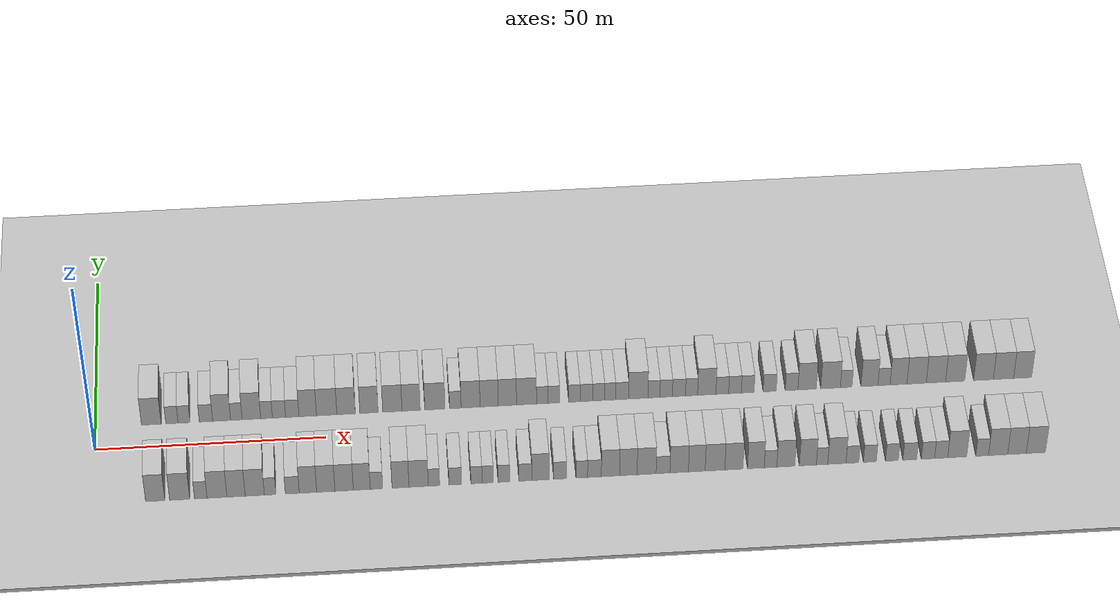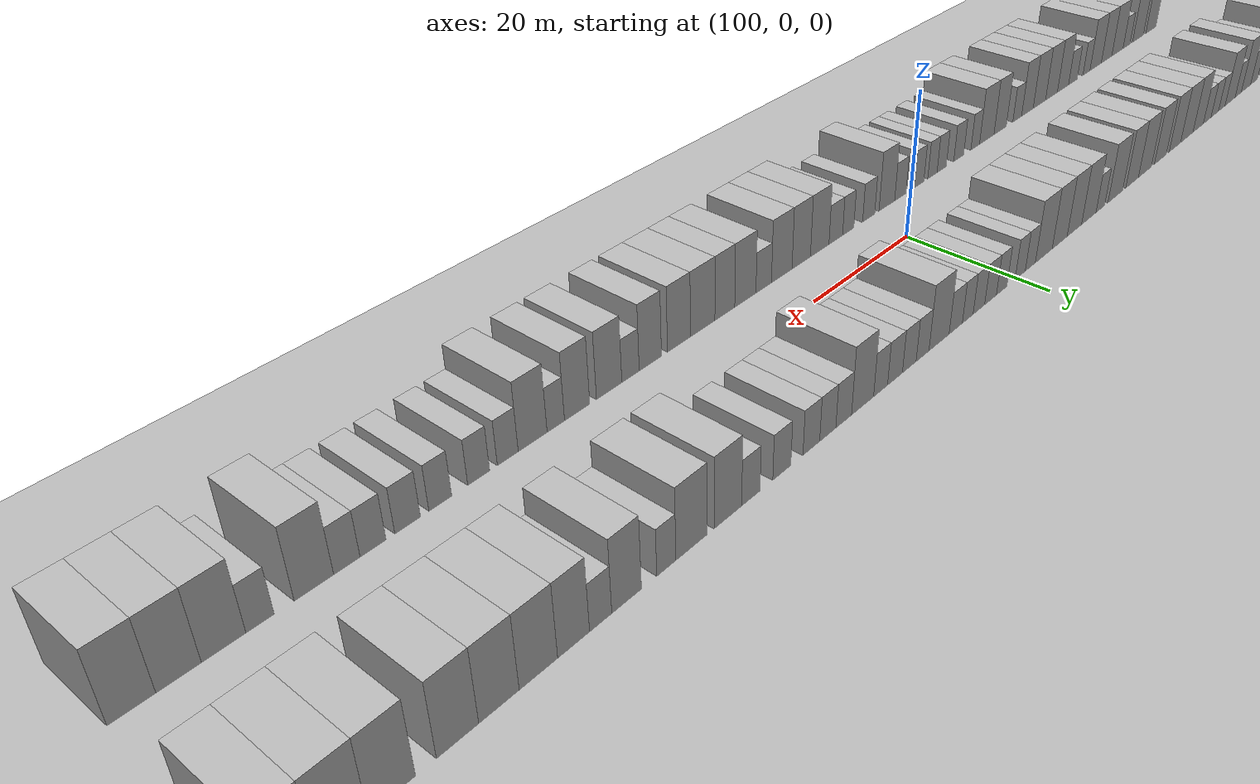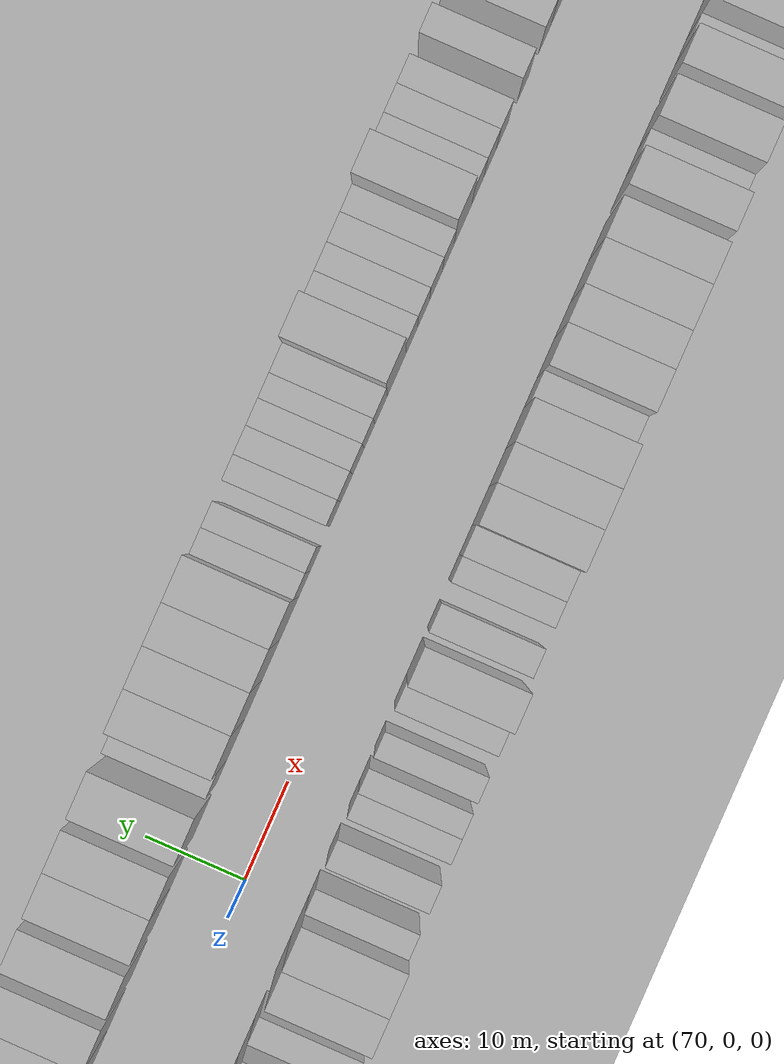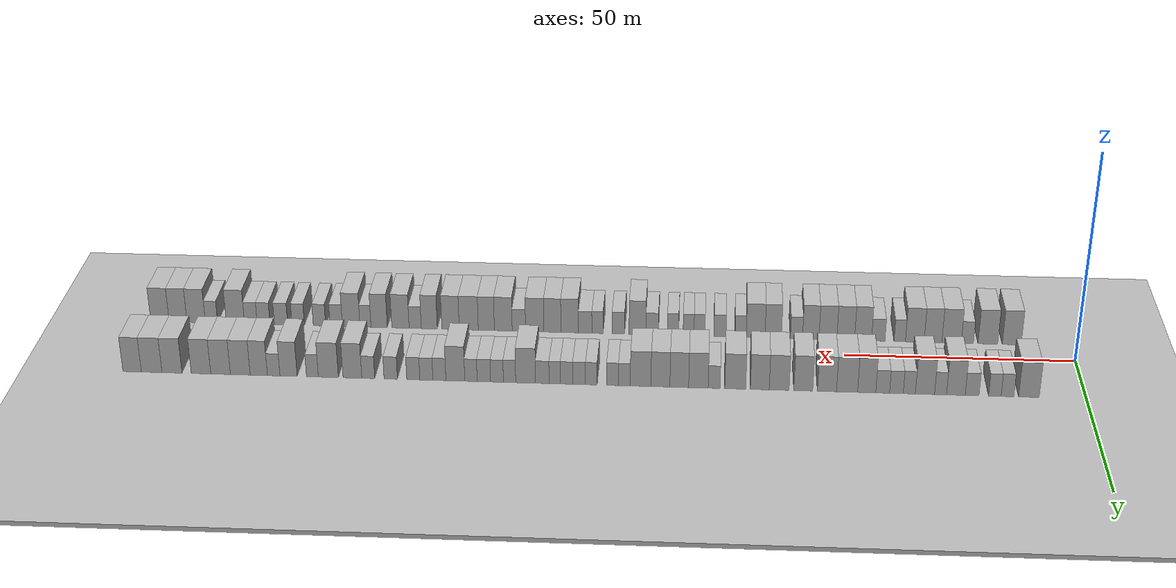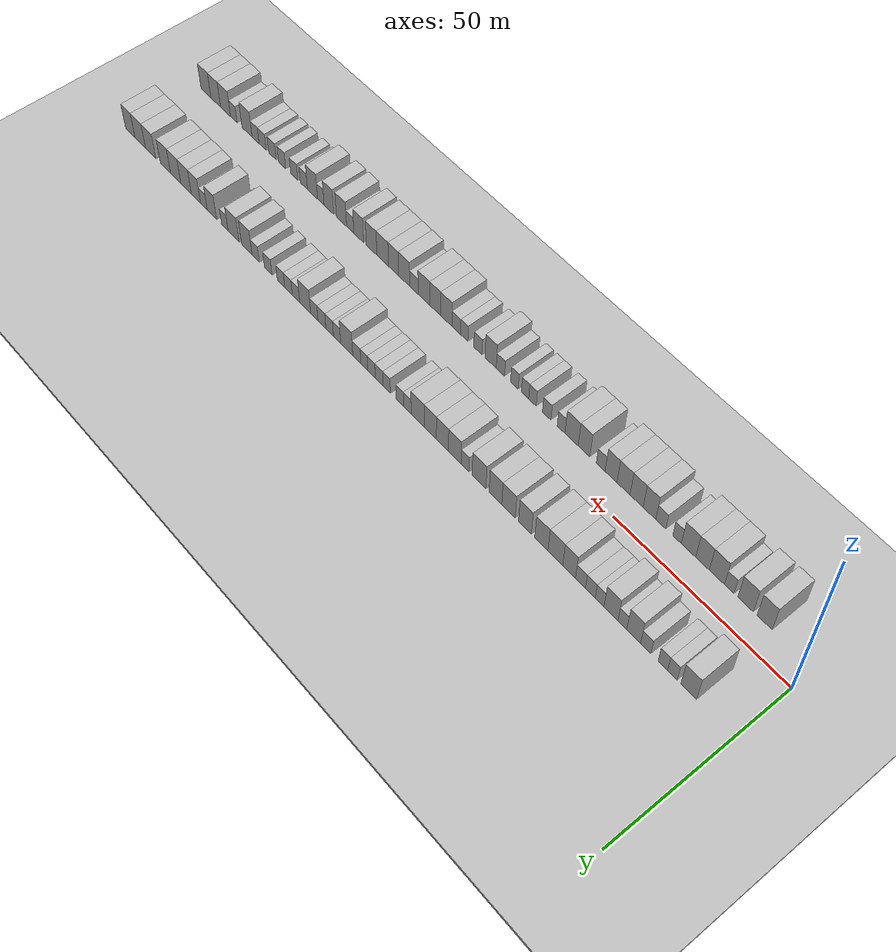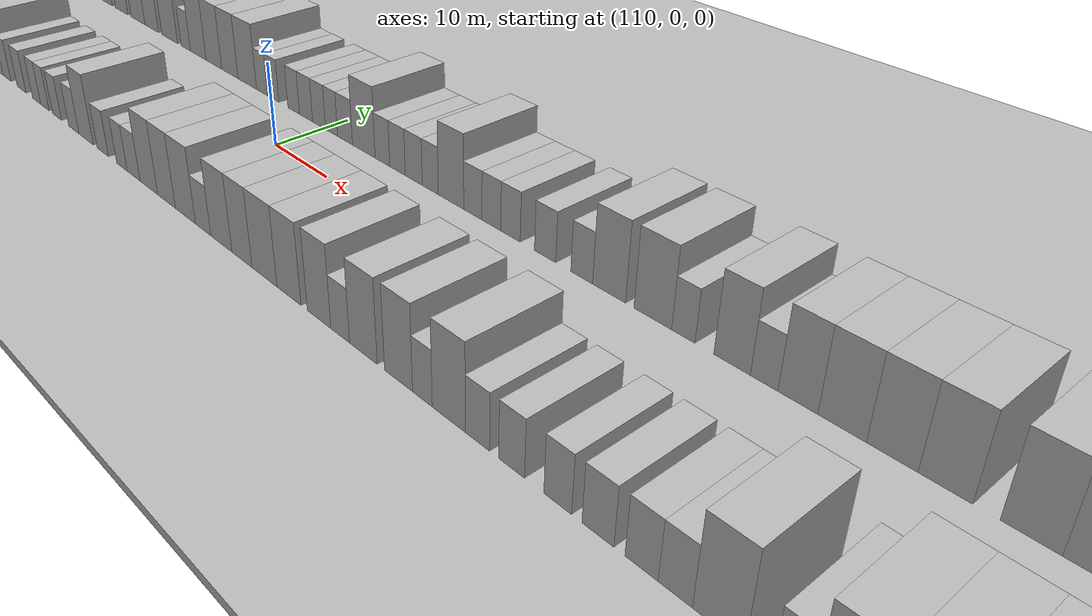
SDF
<?xml version="1.0" encoding="utf-8"?>

<sdf version="1.6">

   <world name="default">

      <gui fullscreen="0">

         <camera name="user_camera">

            <pose>-15 0 4.57585 0 0 0</pose>

            <view_controller>orbit</view_controller>

         </camera>

      </gui>

      <scene>

         <sky>

           <clouds>

             <speed>12</speed>

           </clouds>

         </sky>

         <ambient>0.4 0.4 0.4 1</ambient>

         <background>0.7 0.7 0.7 1</background>

         <shadows>1</shadows>

      </scene>

      <gravity>0 0 -9.8066</gravity>

      <magnetic_field>6e-06 2.3e-05 -4.2e-05</magnetic_field>

      <physics default="0" name="default_physics" type="ode">

         <ode>

            <solver>

               <type>quick</type>

               <iters>10</iters>

               <sor>1.0</sor>

               <use_dynamic_moi_rescaling>0</use_dynamic_moi_rescaling>

            </solver>

            <constraints>

               <cfm>0</cfm>

               <erp>0.2</erp>

               <contact_max_correcting_vel>100</contact_max_correcting_vel>

               <contact_surface_layer>0.001</contact_surface_layer>

            </constraints>

         </ode>

         <max_step_size>0.004</max_step_size>

         <real_time_factor>1</real_time_factor>

         <real_time_update_rate>250</real_time_update_rate>

      </physics>

      <light name="sun" type="directional">

         <cast_shadows>1</cast_shadows>

         <pose>0 0 10 0 0 0</pose>

         <diffuse>0.8 0.8 0.8 1</diffuse>

         <specular>0.2 0.2 0.2 1</specular>

         <attenuation>

            <range>1000</range>

            <constant>0.9</constant>

            <linear>0.01</linear>

            <quadratic>0.001</quadratic>

         </attenuation>

         <direction>-0.5 0.1 -0.9</direction>

      </light>

      <include>

         <name>ground_plane_1</name>

         <uri>model://HANNAS_ground_plane</uri>

         <pose>0 0 0  0 0 0</pose>

      </include>

      <include>

         <name>ground_plane_2</name>

         <uri>model://HANNAS_ground_plane</uri>

         <pose>100 0 0  0 0 0</pose>

      </include>

      <model name="building_1">

         <static>1</static>

         <pose frame="">12.1449 11.0000 0 0.000000 0.000000 1.570796</pose>

         <link name="link">

            <pose frame="">0 0 4.50 0 0 0</pose>

            <collision name="collision">

               <geometry>

                  <box>

                     <size>10.0000 4.2898 9.0000</size>

                  </box>

               </geometry>

               <max_contacts>10</max_contacts>

               <surface>

                  <contact>

                     <ode/>

                  </contact>

                  <bounce/>

                  <friction>

                     <torsional>

                        <ode/>

                     </torsional>

                     <ode/>

                  </friction>

               </surface>

            </collision>

            <visual name="visual">

               <cast_shadows>0</cast_shadows>

               <geometry>

                  <box>

                     <size>10.0000 4.2898 9.0000</size>

                  </box>

               </geometry>

               <material>

                  <script>

                     <uri>model://HANNAS_wall/materials/scripts</uri>

                     <uri>model://HANNAS_wall/materials/textures</uri>

                     <name>vrc/HANNAS_wall</name>

                  </script>

               </material>

            </visual>

            <self_collide>0</self_collide>

            <enable_wind>0</enable_wind>

            <kinematic>0</kinematic>

         </link>

      </model>

      <model name="building_2">

         <static>1</static>

         <pose frame="">16.6229 11.0000 0 0.000000 0.000000 1.570796</pose>

         <link name="link">

            <pose frame="">0 0 3.00 0 0 0</pose>

            <collision name="collision">

               <geometry>

                  <box>

                     <size>10.0000 2.6661 6.0000</size>

                  </box>

               </geometry>

               <max_contacts>10</max_contacts>

               <surface>

                  <contact>

                     <ode/>

                  </contact>

                  <bounce/>

                  <friction>

                     <torsional>

                        <ode/>

                     </torsional>

                     <ode/>

                  </friction>

               </surface>

            </collision>

            <visual name="visual">

               <cast_shadows>0</cast_shadows>

               <geometry>

                  <box>

                     <size>10.0000 2.6661 6.0000</size>

                  </box>

               </geometry>

               <material>

                  <script>

                     <uri>model://HANNAS_wall/materials/scripts</uri>

                     <uri>model://HANNAS_wall/materials/textures</uri>

                     <name>vrc/HANNAS_wall</name>

                  </script>

               </material>

            </visual>

            <self_collide>0</self_collide>

            <enable_wind>0</enable_wind>

            <kinematic>0</kinematic>

         </link>

      </model>

      <model name="building_3">

         <static>1</static>

         <pose frame="">19.2635 11.0000 0 0.000000 0.000000 1.570796</pose>

         <link name="link">

            <pose frame="">0 0 3.00 0 0 0</pose>

            <collision name="collision">

               <geometry>

                  <box>

                     <size>10.0000 2.6152 6.0000</size>

                  </box>

               </geometry>

               <max_contacts>10</max_contacts>

               <surface>

                  <contact>

                     <ode/>

                  </contact>

                  <bounce/>

                  <friction>

                     <torsional>

                        <ode/>

                     </torsional>

                     <ode/>

                  </friction>

               </surface>

            </collision>

            <visual name="visual">

               <cast_shadows>0</cast_shadows>

               <geometry>

                  <box>

                     <size>10.0000 2.6152 6.0000</size>

                  </box>

               </geometry>

               <material>

                  <script>

                     <uri>model://HANNAS_wall/materials/scripts</uri>

                     <uri>model://HANNAS_wall/materials/textures</uri>

                     <name>vrc/HANNAS_wall</name>

                  </script>

               </material>

            </visual>

            <self_collide>0</self_collide>

            <enable_wind>0</enable_wind>

            <kinematic>0</kinematic>

         </link>

      </model>

      <model name="building_4">

         <static>1</static>

         <pose frame="">24.0243 11.0000 0 0.000000 0.000000 1.570796</pose>

         <link name="link">

            <pose frame="">0 0 3.00 0 0 0</pose>

            <collision name="collision">

               <geometry>

                  <box>

                     <size>10.0000 2.9063 6.0000</size>

                  </box>

               </geometry>

               <max_contacts>10</max_contacts>

               <surface>

                  <contact>

                     <ode/>

                  </contact>

                  <bounce/>

                  <friction>

                     <torsional>

                        <ode/>

                     </torsional>

                     <ode/>

                  </friction>

               </surface>

            </collision>

            <visual name="visual">

               <cast_shadows>0</cast_shadows>

               <geometry>

                  <box>

                     <size>10.0000 2.9063 6.0000</size>

                  </box>

               </geometry>

               <material>

                  <script>

                     <uri>model://HANNAS_wall/materials/scripts</uri>

                     <uri>model://HANNAS_wall/materials/textures</uri>

                     <name>vrc/HANNAS_wall</name>

                  </script>

               </material>

            </visual>

            <self_collide>0</self_collide>

            <enable_wind>0</enable_wind>

            <kinematic>0</kinematic>

         </link>

      </model>

      <model name="building_5">

         <static>1</static>

         <pose frame="">27.4322 11.0000 0 0.000000 0.000000 1.570796</pose>

         <link name="link">

            <pose frame="">0 0 4.50 0 0 0</pose>

            <collision name="collision">

               <geometry>

                  <box>

                     <size>10.0000 3.9095 9.0000</size>

                  </box>

               </geometry>

               <max_contacts>10</max_contacts>

               <surface>

                  <contact>

                     <ode/>

                  </contact>

                  <bounce/>

                  <friction>

                     <torsional>

                        <ode/>

                     </torsional>

                     <ode/>

                  </friction>

               </surface>

            </collision>

            <visual name="visual">

               <cast_shadows>0</cast_shadows>

               <geometry>

                  <box>

                     <size>10.0000 3.9095 9.0000</size>

                  </box>

               </geometry>

               <material>

                  <script>

                     <uri>model://HANNAS_wall/materials/scripts</uri>

                     <uri>model://HANNAS_wall/materials/textures</uri>

                     <name>vrc/HANNAS_wall</name>

                  </script>

               </material>

            </visual>

            <self_collide>0</self_collide>

            <enable_wind>0</enable_wind>

            <kinematic>0</kinematic>

         </link>

      </model>

      <model name="building_6">

         <static>1</static>

         <pose frame="">30.6412 11.0000 0 0.000000 0.000000 1.570796</pose>

         <link name="link">

            <pose frame="">0 0 3.00 0 0 0</pose>

            <collision name="collision">

               <geometry>

                  <box>

                     <size>10.0000 2.5084 6.0000</size>

                  </box>

               </geometry>

               <max_contacts>10</max_contacts>

               <surface>

                  <contact>

                     <ode/>

                  </contact>

                  <bounce/>

                  <friction>

                     <torsional>

                        <ode/>

                     </torsional>

                     <ode/>

                  </friction>

               </surface>

            </collision>

            <visual name="visual">

               <cast_shadows>0</cast_shadows>

               <geometry>

                  <box>

                     <size>10.0000 2.5084 6.0000</size>

                  </box>

               </geometry>

               <material>

                  <script>

                     <uri>model://HANNAS_wall/materials/scripts</uri>

                     <uri>model://HANNAS_wall/materials/textures</uri>

                     <name>vrc/HANNAS_wall</name>

                  </script>

               </material>

            </visual>

            <self_collide>0</self_collide>

            <enable_wind>0</enable_wind>

            <kinematic>0</kinematic>

         </link>

      </model>

      <model name="building_7">

         <static>1</static>

         <pose frame="">33.9162 11.0000 0 0.000000 0.000000 1.570796</pose>

         <link name="link">

            <pose frame="">0 0 4.50 0 0 0</pose>

            <collision name="collision">

               <geometry>

                  <box>

                     <size>10.0000 4.0416 9.0000</size>

                  </box>

               </geometry>

               <max_contacts>10</max_contacts>

               <surface>

                  <contact>

                     <ode/>

                  </contact>

                  <bounce/>

                  <friction>

                     <torsional>

                        <ode/>

                     </torsional>

                     <ode/>

                  </friction>

               </surface>

            </collision>

            <visual name="visual">

               <cast_shadows>0</cast_shadows>

               <geometry>

                  <box>

                     <size>10.0000 4.0416 9.0000</size>

                  </box>

               </geometry>

               <material>

                  <script>

                     <uri>model://HANNAS_wall/materials/scripts</uri>

                     <uri>model://HANNAS_wall/materials/textures</uri>

                     <name>vrc/HANNAS_wall</name>

                  </script>

               </material>

            </visual>

            <self_collide>0</self_collide>

            <enable_wind>0</enable_wind>

            <kinematic>0</kinematic>

         </link>

      </model>

      <model name="building_8">

         <static>1</static>

         <pose frame="">37.2105 11.0000 0 0.000000 0.000000 1.570796</pose>

         <link name="link">

            <pose frame="">0 0 3.00 0 0 0</pose>

            <collision name="collision">

               <geometry>

                  <box>

                     <size>10.0000 2.5469 6.0000</size>

                  </box>

               </geometry>

               <max_contacts>10</max_contacts>

               <surface>

                  <contact>

                     <ode/>

                  </contact>

                  <bounce/>

                  <friction>

                     <torsional>

                        <ode/>

                     </torsional>

                     <ode/>

                  </friction>

               </surface>

            </collision>

            <visual name="visual">

               <cast_shadows>0</cast_shadows>

               <geometry>

                  <box>

                     <size>10.0000 2.5469 6.0000</size>

                  </box>

               </geometry>

               <material>

                  <script>

                     <uri>model://HANNAS_wall/materials/scripts</uri>

                     <uri>model://HANNAS_wall/materials/textures</uri>

                     <name>vrc/HANNAS_wall</name>

                  </script>

               </material>

            </visual>

            <self_collide>0</self_collide>

            <enable_wind>0</enable_wind>

            <kinematic>0</kinematic>

         </link>

      </model>

      <model name="building_9">

         <static>1</static>

         <pose frame="">39.9232 11.0000 0 0.000000 0.000000 1.570796</pose>

         <link name="link">

            <pose frame="">0 0 3.00 0 0 0</pose>

            <collision name="collision">

               <geometry>

                  <box>

                     <size>10.0000 2.8787 6.0000</size>

                  </box>

               </geometry>

               <max_contacts>10</max_contacts>

               <surface>

                  <contact>

                     <ode/>

                  </contact>

                  <bounce/>

                  <friction>

                     <torsional>

                        <ode/>

                     </torsional>

                     <ode/>

                  </friction>

               </surface>

            </collision>

            <visual name="visual">

               <cast_shadows>0</cast_shadows>

               <geometry>

                  <box>

                     <size>10.0000 2.8787 6.0000</size>

                  </box>

               </geometry>

               <material>

                  <script>

                     <uri>model://HANNAS_wall/materials/scripts</uri>

                     <uri>model://HANNAS_wall/materials/textures</uri>

                     <name>vrc/HANNAS_wall</name>

                  </script>

               </material>

            </visual>

            <self_collide>0</self_collide>

            <enable_wind>0</enable_wind>

            <kinematic>0</kinematic>

         </link>

      </model>

      <model name="building_10">

         <static>1</static>

         <pose frame="">42.8151 11.0000 0 0.000000 0.000000 1.570796</pose>

         <link name="link">

            <pose frame="">0 0 3.00 0 0 0</pose>

            <collision name="collision">

               <geometry>

                  <box>

                     <size>10.0000 2.9050 6.0000</size>

                  </box>

               </geometry>

               <max_contacts>10</max_contacts>

               <surface>

                  <contact>

                     <ode/>

                  </contact>

                  <bounce/>

                  <friction>

                     <torsional>

                        <ode/>

                     </torsional>

                     <ode/>

                  </friction>

               </surface>

            </collision>

            <visual name="visual">

               <cast_shadows>0</cast_shadows>

               <geometry>

                  <box>

                     <size>10.0000 2.9050 6.0000</size>

                  </box>

               </geometry>

               <material>

                  <script>

                     <uri>model://HANNAS_wall/materials/scripts</uri>

                     <uri>model://HANNAS_wall/materials/textures</uri>

                     <name>vrc/HANNAS_wall</name>

                  </script>

               </material>

            </visual>

            <self_collide>0</self_collide>

            <enable_wind>0</enable_wind>

            <kinematic>0</kinematic>

         </link>

      </model>

      <model name="building_11">

         <static>1</static>

         <pose frame="">46.1781 11.0000 0 0.000000 0.000000 1.570796</pose>

         <link name="link">

            <pose frame="">0 0 4.50 0 0 0</pose>

            <collision name="collision">

               <geometry>

                  <box>

                     <size>10.0000 3.8211 9.0000</size>

                  </box>

               </geometry>

               <max_contacts>10</max_contacts>

               <surface>

                  <contact>

                     <ode/>

                  </contact>

                  <bounce/>

                  <friction>

                     <torsional>

                        <ode/>

                     </torsional>

                     <ode/>

                  </friction>

               </surface>

            </collision>

            <visual name="visual">

               <cast_shadows>0</cast_shadows>

               <geometry>

                  <box>

                     <size>10.0000 3.8211 9.0000</size>

                  </box>

               </geometry>

               <material>

                  <script>

                     <uri>model://HANNAS_wall/materials/scripts</uri>

                     <uri>model://HANNAS_wall/materials/textures</uri>

                     <name>vrc/HANNAS_wall</name>

                  </script>

               </material>

            </visual>

            <self_collide>0</self_collide>

            <enable_wind>0</enable_wind>

            <kinematic>0</kinematic>

         </link>

      </model>

      <model name="building_12">

         <static>1</static>

         <pose frame="">50.3115 11.0000 0 0.000000 0.000000 1.570796</pose>

         <link name="link">

            <pose frame="">0 0 4.50 0 0 0</pose>

            <collision name="collision">

               <geometry>

                  <box>

                     <size>10.0000 4.4456 9.0000</size>

                  </box>

               </geometry>

               <max_contacts>10</max_contacts>

               <surface>

                  <contact>

                     <ode/>

                  </contact>

                  <bounce/>

                  <friction>

                     <torsional>

                        <ode/>

                     </torsional>

                     <ode/>

                  </friction>

               </surface>

            </collision>

            <visual name="visual">

               <cast_shadows>0</cast_shadows>

               <geometry>

                  <box>

                     <size>10.0000 4.4456 9.0000</size>

                  </box>

               </geometry>

               <material>

                  <script>

                     <uri>model://HANNAS_wall/materials/scripts</uri>

                     <uri>model://HANNAS_wall/materials/textures</uri>

                     <name>vrc/HANNAS_wall</name>

                  </script>

               </material>

            </visual>

            <self_collide>0</self_collide>

            <enable_wind>0</enable_wind>

            <kinematic>0</kinematic>

         </link>

      </model>

      <model name="building_13">

         <static>1</static>

         <pose frame="">54.5443 11.0000 0 0.000000 0.000000 1.570796</pose>

         <link name="link">

            <pose frame="">0 0 4.50 0 0 0</pose>

            <collision name="collision">

               <geometry>

                  <box>

                     <size>10.0000 4.0202 9.0000</size>

                  </box>

               </geometry>

               <max_contacts>10</max_contacts>

               <surface>

                  <contact>

                     <ode/>

                  </contact>

                  <bounce/>

                  <friction>

                     <torsional>

                        <ode/>

                     </torsional>

                     <ode/>

                  </friction>

               </surface>

            </collision>

            <visual name="visual">

               <cast_shadows>0</cast_shadows>

               <geometry>

                  <box>

                     <size>10.0000 4.0202 9.0000</size>

                  </box>

               </geometry>

               <material>

                  <script>

                     <uri>model://HANNAS_wall/materials/scripts</uri>

                     <uri>model://HANNAS_wall/materials/textures</uri>

                     <name>vrc/HANNAS_wall</name>

                  </script>

               </material>

            </visual>

            <self_collide>0</self_collide>

            <enable_wind>0</enable_wind>

            <kinematic>0</kinematic>

         </link>

      </model>

      <model name="building_14">

         <static>1</static>

         <pose frame="">59.5513 11.0000 0 0.000000 0.000000 1.570796</pose>

         <link name="link">

            <pose frame="">0 0 4.50 0 0 0</pose>

            <collision name="collision">

               <geometry>

                  <box>

                     <size>10.0000 3.9937 9.0000</size>

                  </box>

               </geometry>

               <max_contacts>10</max_contacts>

               <surface>

                  <contact>

                     <ode/>

                  </contact>

                  <bounce/>

                  <friction>

                     <torsional>

                        <ode/>

                     </torsional>

                     <ode/>

                  </friction>

               </surface>

            </collision>

            <visual name="visual">

               <cast_shadows>0</cast_shadows>

               <geometry>

                  <box>

                     <size>10.0000 3.9937 9.0000</size>

                  </box>

               </geometry>

               <material>

                  <script>

                     <uri>model://HANNAS_wall/materials/scripts</uri>

                     <uri>model://HANNAS_wall/materials/textures</uri>

                     <name>vrc/HANNAS_wall</name>

                  </script>

               </material>

            </visual>

            <self_collide>0</self_collide>

            <enable_wind>0</enable_wind>

            <kinematic>0</kinematic>

         </link>

      </model>

      <model name="building_15">

         <static>1</static>

         <pose frame="">64.6542 11.0000 0 0.000000 0.000000 1.570796</pose>

         <link name="link">

            <pose frame="">0 0 4.50 0 0 0</pose>

            <collision name="collision">

               <geometry>

                  <box>

                     <size>10.0000 4.2122 9.0000</size>

                  </box>

               </geometry>

               <max_contacts>10</max_contacts>

               <surface>

                  <contact>

                     <ode/>

                  </contact>

                  <bounce/>

                  <friction>

                     <torsional>

                        <ode/>

                     </torsional>

                     <ode/>

                  </friction>

               </surface>

            </collision>

            <visual name="visual">

               <cast_shadows>0</cast_shadows>

               <geometry>

                  <box>

                     <size>10.0000 4.2122 9.0000</size>

                  </box>

               </geometry>

               <material>

                  <script>

                     <uri>model://HANNAS_wall/materials/scripts</uri>

                     <uri>model://HANNAS_wall/materials/textures</uri>

                     <name>vrc/HANNAS_wall</name>

                  </script>

               </material>

            </visual>

            <self_collide>0</self_collide>

            <enable_wind>0</enable_wind>

            <kinematic>0</kinematic>

         </link>

      </model>

      <model name="building_16">

         <static>1</static>

         <pose frame="">68.7493 11.0000 0 0.000000 0.000000 1.570796</pose>

         <link name="link">

            <pose frame="">0 0 4.50 0 0 0</pose>

            <collision name="collision">

               <geometry>

                  <box>

                     <size>10.0000 3.9779 9.0000</size>

                  </box>

               </geometry>

               <max_contacts>10</max_contacts>

               <surface>

                  <contact>

                     <ode/>

                  </contact>

                  <bounce/>

                  <friction>

                     <torsional>

                        <ode/>

                     </torsional>

                     <ode/>

                  </friction>

               </surface>

            </collision>

            <visual name="visual">

               <cast_shadows>0</cast_shadows>

               <geometry>

                  <box>

                     <size>10.0000 3.9779 9.0000</size>

                  </box>

               </geometry>

               <material>

                  <script>

                     <uri>model://HANNAS_wall/materials/scripts</uri>

                     <uri>model://HANNAS_wall/materials/textures</uri>

                     <name>vrc/HANNAS_wall</name>

                  </script>

               </material>

            </visual>

            <self_collide>0</self_collide>

            <enable_wind>0</enable_wind>

            <kinematic>0</kinematic>

         </link>

      </model>

      <model name="building_17">

         <static>1</static>

         <pose frame="">73.9517 11.0000 0 0.000000 0.000000 1.570796</pose>

         <link name="link">

            <pose frame="">0 0 4.50 0 0 0</pose>

            <collision name="collision">

               <geometry>

                  <box>

                     <size>10.0000 4.4268 9.0000</size>

                  </box>

               </geometry>

               <max_contacts>10</max_contacts>

               <surface>

                  <contact>

                     <ode/>

                  </contact>

                  <bounce/>

                  <friction>

                     <torsional>

                        <ode/>

                     </torsional>

                     <ode/>

                  </friction>

               </surface>

            </collision>

            <visual name="visual">

               <cast_shadows>0</cast_shadows>

               <geometry>

                  <box>

                     <size>10.0000 4.4268 9.0000</size>

                  </box>

               </geometry>

               <material>

                  <script>

                     <uri>model://HANNAS_wall/materials/scripts</uri>

                     <uri>model://HANNAS_wall/materials/textures</uri>

                     <name>vrc/HANNAS_wall</name>

                  </script>

               </material>

            </visual>

            <self_collide>0</self_collide>

            <enable_wind>0</enable_wind>

            <kinematic>0</kinematic>

         </link>

      </model>

      <model name="building_18">

         <static>1</static>

         <pose frame="">78.4234 11.0000 0 0.000000 0.000000 1.570796</pose>

         <link name="link">

            <pose frame="">0 0 3.00 0 0 0</pose>

            <collision name="collision">

               <geometry>

                  <box>

                     <size>10.0000 2.5167 6.0000</size>

                  </box>

               </geometry>

               <max_contacts>10</max_contacts>

               <surface>

                  <contact>

                     <ode/>

                  </contact>

                  <bounce/>

                  <friction>

                     <torsional>

                        <ode/>

                     </torsional>

                     <ode/>

                  </friction>

               </surface>

            </collision>

            <visual name="visual">

               <cast_shadows>0</cast_shadows>

               <geometry>

                  <box>

                     <size>10.0000 2.5167 6.0000</size>

                  </box>

               </geometry>

               <material>

                  <script>

                     <uri>model://HANNAS_wall/materials/scripts</uri>

                     <uri>model://HANNAS_wall/materials/textures</uri>

                     <name>vrc/HANNAS_wall</name>

                  </script>

               </material>

            </visual>

            <self_collide>0</self_collide>

            <enable_wind>0</enable_wind>

            <kinematic>0</kinematic>

         </link>

      </model>

      <model name="building_19">

         <static>1</static>

         <pose frame="">81.7531 11.0000 0 0.000000 0.000000 1.570796</pose>

         <link name="link">

            <pose frame="">0 0 4.50 0 0 0</pose>

            <collision name="collision">

               <geometry>

                  <box>

                     <size>10.0000 4.1428 9.0000</size>

                  </box>

               </geometry>

               <max_contacts>10</max_contacts>

               <surface>

                  <contact>

                     <ode/>

                  </contact>

                  <bounce/>

                  <friction>

                     <torsional>

                        <ode/>

                     </torsional>

                     <ode/>

                  </friction>

               </surface>

            </collision>

            <visual name="visual">

               <cast_shadows>0</cast_shadows>

               <geometry>

                  <box>

                     <size>10.0000 4.1428 9.0000</size>

                  </box>

               </geometry>

               <material>

                  <script>

                     <uri>model://HANNAS_wall/materials/scripts</uri>

                     <uri>model://HANNAS_wall/materials/textures</uri>

                     <name>vrc/HANNAS_wall</name>

                  </script>

               </material>

            </visual>

            <self_collide>0</self_collide>

            <enable_wind>0</enable_wind>

            <kinematic>0</kinematic>

         </link>

      </model>

      <model name="building_20">

         <static>1</static>

         <pose frame="">85.8169 11.0000 0 0.000000 0.000000 1.570796</pose>

         <link name="link">

            <pose frame="">0 0 4.50 0 0 0</pose>

            <collision name="collision">

               <geometry>

                  <box>

                     <size>10.0000 3.9847 9.0000</size>

                  </box>

               </geometry>

               <max_contacts>10</max_contacts>

               <surface>

                  <contact>

                     <ode/>

                  </contact>

                  <bounce/>

                  <friction>

                     <torsional>

                        <ode/>

                     </torsional>

                     <ode/>

                  </friction>

               </surface>

            </collision>

            <visual name="visual">

               <cast_shadows>0</cast_shadows>

               <geometry>

                  <box>

                     <size>10.0000 3.9847 9.0000</size>

                  </box>

               </geometry>

               <material>

                  <script>

                     <uri>model://HANNAS_wall/materials/scripts</uri>

                     <uri>model://HANNAS_wall/materials/textures</uri>

                     <name>vrc/HANNAS_wall</name>

                  </script>

               </material>

            </visual>

            <self_collide>0</self_collide>

            <enable_wind>0</enable_wind>

            <kinematic>0</kinematic>

         </link>

      </model>

      <model name="building_21">

         <static>1</static>

         <pose frame="">89.8187 11.0000 0 0.000000 0.000000 1.570796</pose>

         <link name="link">

            <pose frame="">0 0 4.50 0 0 0</pose>

            <collision name="collision">

               <geometry>

                  <box>

                     <size>10.0000 4.0189 9.0000</size>

                  </box>

               </geometry>

               <max_contacts>10</max_contacts>

               <surface>

                  <contact>

                     <ode/>

                  </contact>

                  <bounce/>

                  <friction>

                     <torsional>

                        <ode/>

                     </torsional>

                     <ode/>

                  </friction>

               </surface>

            </collision>

            <visual name="visual">

               <cast_shadows>0</cast_shadows>

               <geometry>

                  <box>

                     <size>10.0000 4.0189 9.0000</size>

                  </box>

               </geometry>

               <material>

                  <script>

                     <uri>model://HANNAS_wall/materials/scripts</uri>

                     <uri>model://HANNAS_wall/materials/textures</uri>

                     <name>vrc/HANNAS_wall</name>

                  </script>

               </material>

            </visual>

            <self_collide>0</self_collide>

            <enable_wind>0</enable_wind>

            <kinematic>0</kinematic>

         </link>

      </model>

      <model name="building_22">

         <static>1</static>

         <pose frame="">94.0223 11.0000 0 0.000000 0.000000 1.570796</pose>

         <link name="link">

            <pose frame="">0 0 4.50 0 0 0</pose>

            <collision name="collision">

               <geometry>

                  <box>

                     <size>10.0000 4.3884 9.0000</size>

                  </box>

               </geometry>

               <max_contacts>10</max_contacts>

               <surface>

                  <contact>

                     <ode/>

                  </contact>

                  <bounce/>

                  <friction>

                     <torsional>

                        <ode/>

                     </torsional>

                     <ode/>

                  </friction>

               </surface>

            </collision>

            <visual name="visual">

               <cast_shadows>0</cast_shadows>

               <geometry>

                  <box>

                     <size>10.0000 4.3884 9.0000</size>

                  </box>

               </geometry>

               <material>

                  <script>

                     <uri>model://HANNAS_wall/materials/scripts</uri>

                     <uri>model://HANNAS_wall/materials/textures</uri>

                     <name>vrc/HANNAS_wall</name>

                  </script>

               </material>

            </visual>

            <self_collide>0</self_collide>

            <enable_wind>0</enable_wind>

            <kinematic>0</kinematic>

         </link>

      </model>

      <model name="building_23">

         <static>1</static>

         <pose frame="">97.4901 11.0000 0 0.000000 0.000000 1.570796</pose>

         <link name="link">

            <pose frame="">0 0 3.00 0 0 0</pose>

            <collision name="collision">

               <geometry>

                  <box>

                     <size>10.0000 2.5473 6.0000</size>

                  </box>

               </geometry>

               <max_contacts>10</max_contacts>

               <surface>

                  <contact>

                     <ode/>

                  </contact>

                  <bounce/>

                  <friction>

                     <torsional>

                        <ode/>

                     </torsional>

                     <ode/>

                  </friction>

               </surface>

            </collision>

            <visual name="visual">

               <cast_shadows>0</cast_shadows>

               <geometry>

                  <box>

                     <size>10.0000 2.5473 6.0000</size>

                  </box>

               </geometry>

               <material>

                  <script>

                     <uri>model://HANNAS_wall/materials/scripts</uri>

                     <uri>model://HANNAS_wall/materials/textures</uri>

                     <name>vrc/HANNAS_wall</name>

                  </script>

               </material>

            </visual>

            <self_collide>0</self_collide>

            <enable_wind>0</enable_wind>

            <kinematic>0</kinematic>

         </link>

      </model>

      <model name="building_24">

         <static>1</static>

         <pose frame="">100.0293 11.0000 0 0.000000 0.000000 1.570796</pose>

         <link name="link">

            <pose frame="">0 0 3.00 0 0 0</pose>

            <collision name="collision">

               <geometry>

                  <box>

                     <size>10.0000 2.5309 6.0000</size>

                  </box>

               </geometry>

               <max_contacts>10</max_contacts>

               <surface>

                  <contact>

                     <ode/>

                  </contact>

                  <bounce/>

                  <friction>

                     <torsional>

                        <ode/>

                     </torsional>

                     <ode/>

                  </friction>

               </surface>

            </collision>

            <visual name="visual">

               <cast_shadows>0</cast_shadows>

               <geometry>

                  <box>

                     <size>10.0000 2.5309 6.0000</size>

                  </box>

               </geometry>

               <material>

                  <script>

                     <uri>model://HANNAS_wall/materials/scripts</uri>

                     <uri>model://HANNAS_wall/materials/textures</uri>

                     <name>vrc/HANNAS_wall</name>

                  </script>

               </material>

            </visual>

            <self_collide>0</self_collide>

            <enable_wind>0</enable_wind>

            <kinematic>0</kinematic>

         </link>

      </model>

      <model name="building_25">

         <static>1</static>

         <pose frame="">104.5352 11.0000 0 0.000000 0.000000 1.570796</pose>

         <link name="link">

            <pose frame="">0 0 3.00 0 0 0</pose>

            <collision name="collision">

               <geometry>

                  <box>

                     <size>10.0000 2.4810 6.0000</size>

                  </box>

               </geometry>

               <max_contacts>10</max_contacts>

               <surface>

                  <contact>

                     <ode/>

                  </contact>

                  <bounce/>

                  <friction>

                     <torsional>

                        <ode/>

                     </torsional>

                     <ode/>

                  </friction>

               </surface>

            </collision>

            <visual name="visual">

               <cast_shadows>0</cast_shadows>

               <geometry>

                  <box>

                     <size>10.0000 2.4810 6.0000</size>

                  </box>

               </geometry>

               <material>

                  <script>

                     <uri>model://HANNAS_wall/materials/scripts</uri>

                     <uri>model://HANNAS_wall/materials/textures</uri>

                     <name>vrc/HANNAS_wall</name>

                  </script>

               </material>

            </visual>

            <self_collide>0</self_collide>

            <enable_wind>0</enable_wind>

            <kinematic>0</kinematic>

         </link>

      </model>

      <model name="building_26">

         <static>1</static>

         <pose frame="">107.1506 11.0000 0 0.000000 0.000000 1.570796</pose>

         <link name="link">

            <pose frame="">0 0 3.00 0 0 0</pose>

            <collision name="collision">

               <geometry>

                  <box>

                     <size>10.0000 2.7499 6.0000</size>

                  </box>

               </geometry>

               <max_contacts>10</max_contacts>

               <surface>

                  <contact>

                     <ode/>

                  </contact>

                  <bounce/>

                  <friction>

                     <torsional>

                        <ode/>

                     </torsional>

                     <ode/>

                  </friction>

               </surface>

            </collision>

            <visual name="visual">

               <cast_shadows>0</cast_shadows>

               <geometry>

                  <box>

                     <size>10.0000 2.7499 6.0000</size>

                  </box>

               </geometry>

               <material>

                  <script>

                     <uri>model://HANNAS_wall/materials/scripts</uri>

                     <uri>model://HANNAS_wall/materials/textures</uri>

                     <name>vrc/HANNAS_wall</name>

                  </script>

               </material>

            </visual>

            <self_collide>0</self_collide>

            <enable_wind>0</enable_wind>

            <kinematic>0</kinematic>

         </link>

      </model>

      <model name="building_27">

         <static>1</static>

         <pose frame="">109.8385 11.0000 0 0.000000 0.000000 1.570796</pose>

         <link name="link">

            <pose frame="">0 0 3.00 0 0 0</pose>

            <collision name="collision">

               <geometry>

                  <box>

                     <size>10.0000 2.6257 6.0000</size>

                  </box>

               </geometry>

               <max_contacts>10</max_contacts>

               <surface>

                  <contact>

                     <ode/>

                  </contact>

                  <bounce/>

                  <friction>

                     <torsional>

                        <ode/>

                     </torsional>

                     <ode/>

                  </friction>

               </surface>

            </collision>

            <visual name="visual">

               <cast_shadows>0</cast_shadows>

               <geometry>

                  <box>

                     <size>10.0000 2.6257 6.0000</size>

                  </box>

               </geometry>

               <material>

                  <script>

                     <uri>model://HANNAS_wall/materials/scripts</uri>

                     <uri>model://HANNAS_wall/materials/textures</uri>

                     <name>vrc/HANNAS_wall</name>

                  </script>

               </material>

            </visual>

            <self_collide>0</self_collide>

            <enable_wind>0</enable_wind>

            <kinematic>0</kinematic>

         </link>

      </model>

      <model name="building_28">

         <static>1</static>

         <pose frame="">112.3581 11.0000 0 0.000000 0.000000 1.570796</pose>

         <link name="link">

            <pose frame="">0 0 3.00 0 0 0</pose>

            <collision name="collision">

               <geometry>

                  <box>

                     <size>10.0000 2.4136 6.0000</size>

                  </box>

               </geometry>

               <max_contacts>10</max_contacts>

               <surface>

                  <contact>

                     <ode/>

                  </contact>

                  <bounce/>

                  <friction>

                     <torsional>

                        <ode/>

                     </torsional>

                     <ode/>

                  </friction>

               </surface>

            </collision>

            <visual name="visual">

               <cast_shadows>0</cast_shadows>

               <geometry>

                  <box>

                     <size>10.0000 2.4136 6.0000</size>

                  </box>

               </geometry>

               <material>

                  <script>

                     <uri>model://HANNAS_wall/materials/scripts</uri>

                     <uri>model://HANNAS_wall/materials/textures</uri>

                     <name>vrc/HANNAS_wall</name>

                  </script>

               </material>

            </visual>

            <self_collide>0</self_collide>

            <enable_wind>0</enable_wind>

            <kinematic>0</kinematic>

         </link>

      </model>

      <model name="building_29">

         <static>1</static>

         <pose frame="">115.0094 11.0000 0 0.000000 0.000000 1.570796</pose>

         <link name="link">

            <pose frame="">0 0 3.00 0 0 0</pose>

            <collision name="collision">

               <geometry>

                  <box>

                     <size>10.0000 2.8890 6.0000</size>

                  </box>

               </geometry>

               <max_contacts>10</max_contacts>

               <surface>

                  <contact>

                     <ode/>

                  </contact>

                  <bounce/>

                  <friction>

                     <torsional>

                        <ode/>

                     </torsional>

                     <ode/>

                  </friction>

               </surface>

            </collision>

            <visual name="visual">

               <cast_shadows>0</cast_shadows>

               <geometry>

                  <box>

                     <size>10.0000 2.8890 6.0000</size>

                  </box>

               </geometry>

               <material>

                  <script>

                     <uri>model://HANNAS_wall/materials/scripts</uri>

                     <uri>model://HANNAS_wall/materials/textures</uri>

                     <name>vrc/HANNAS_wall</name>

                  </script>

               </material>

            </visual>

            <self_collide>0</self_collide>

            <enable_wind>0</enable_wind>

            <kinematic>0</kinematic>

         </link>

      </model>

      <model name="building_30">

         <static>1</static>

         <pose frame="">118.5766 11.0000 0 0.000000 0.000000 1.570796</pose>

         <link name="link">

            <pose frame="">0 0 4.50 0 0 0</pose>

            <collision name="collision">

               <geometry>

                  <box>

                     <size>10.0000 4.2454 9.0000</size>

                  </box>

               </geometry>

               <max_contacts>10</max_contacts>

               <surface>

                  <contact>

                     <ode/>

                  </contact>

                  <bounce/>

                  <friction>

                     <torsional>

                        <ode/>

                     </torsional>

                     <ode/>

                  </friction>

               </surface>

            </collision>

            <visual name="visual">

               <cast_shadows>0</cast_shadows>

               <geometry>

                  <box>

                     <size>10.0000 4.2454 9.0000</size>

                  </box>

               </geometry>

               <material>

                  <script>

                     <uri>model://HANNAS_wall/materials/scripts</uri>

                     <uri>model://HANNAS_wall/materials/textures</uri>

                     <name>vrc/HANNAS_wall</name>

                  </script>

               </material>

            </visual>

            <self_collide>0</self_collide>

            <enable_wind>0</enable_wind>

            <kinematic>0</kinematic>

         </link>

      </model>

      <model name="building_31">

         <static>1</static>

         <pose frame="">122.0176 11.0000 0 0.000000 0.000000 1.570796</pose>

         <link name="link">

            <pose frame="">0 0 3.00 0 0 0</pose>

            <collision name="collision">

               <geometry>

                  <box>

                     <size>10.0000 2.6364 6.0000</size>

                  </box>

               </geometry>

               <max_contacts>10</max_contacts>

               <surface>

                  <contact>

                     <ode/>

                  </contact>

                  <bounce/>

                  <friction>

                     <torsional>

                        <ode/>

                     </torsional>

                     <ode/>

                  </friction>

               </surface>

            </collision>

            <visual name="visual">

               <cast_shadows>0</cast_shadows>

               <geometry>

                  <box>

                     <size>10.0000 2.6364 6.0000</size>

                  </box>

               </geometry>

               <material>

                  <script>

                     <uri>model://HANNAS_wall/materials/scripts</uri>

                     <uri>model://HANNAS_wall/materials/textures</uri>

                     <name>vrc/HANNAS_wall</name>

                  </script>

               </material>

            </visual>

            <self_collide>0</self_collide>

            <enable_wind>0</enable_wind>

            <kinematic>0</kinematic>

         </link>

      </model>

      <model name="building_32">

         <static>1</static>

         <pose frame="">124.7056 11.0000 0 0.000000 0.000000 1.570796</pose>

         <link name="link">

            <pose frame="">0 0 3.00 0 0 0</pose>

            <collision name="collision">

               <geometry>

                  <box>

                     <size>10.0000 2.7395 6.0000</size>

                  </box>

               </geometry>

               <max_contacts>10</max_contacts>

               <surface>

                  <contact>

                     <ode/>

                  </contact>

                  <bounce/>

                  <friction>

                     <torsional>

                        <ode/>

                     </torsional>

                     <ode/>

                  </friction>

               </surface>

            </collision>

            <visual name="visual">

               <cast_shadows>0</cast_shadows>

               <geometry>

                  <box>

                     <size>10.0000 2.7395 6.0000</size>

                  </box>

               </geometry>

               <material>

                  <script>

                     <uri>model://HANNAS_wall/materials/scripts</uri>

                     <uri>model://HANNAS_wall/materials/textures</uri>

                     <name>vrc/HANNAS_wall</name>

                  </script>

               </material>

            </visual>

            <self_collide>0</self_collide>

            <enable_wind>0</enable_wind>

            <kinematic>0</kinematic>

         </link>

      </model>

      <model name="building_33">

         <static>1</static>

         <pose frame="">127.5214 11.0000 0 0.000000 0.000000 1.570796</pose>

         <link name="link">

            <pose frame="">0 0 3.00 0 0 0</pose>

            <collision name="collision">

               <geometry>

                  <box>

                     <size>10.0000 2.8920 6.0000</size>

                  </box>

               </geometry>

               <max_contacts>10</max_contacts>

               <surface>

                  <contact>

                     <ode/>

                  </contact>

                  <bounce/>

                  <friction>

                     <torsional>

                        <ode/>

                     </torsional>

                     <ode/>

                  </friction>

               </surface>

            </collision>

            <visual name="visual">

               <cast_shadows>0</cast_shadows>

               <geometry>

                  <box>

                     <size>10.0000 2.8920 6.0000</size>

                  </box>

               </geometry>

               <material>

                  <script>

                     <uri>model://HANNAS_wall/materials/scripts</uri>

                     <uri>model://HANNAS_wall/materials/textures</uri>

                     <name>vrc/HANNAS_wall</name>

                  </script>

               </material>

            </visual>

            <self_collide>0</self_collide>

            <enable_wind>0</enable_wind>

            <kinematic>0</kinematic>

         </link>

      </model>

      <model name="building_34">

         <static>1</static>

         <pose frame="">130.2917 11.0000 0 0.000000 0.000000 1.570796</pose>

         <link name="link">

            <pose frame="">0 0 3.00 0 0 0</pose>

            <collision name="collision">

               <geometry>

                  <box>

                     <size>10.0000 2.6486 6.0000</size>

                  </box>

               </geometry>

               <max_contacts>10</max_contacts>

               <surface>

                  <contact>

                     <ode/>

                  </contact>

                  <bounce/>

                  <friction>

                     <torsional>

                        <ode/>

                     </torsional>

                     <ode/>

                  </friction>

               </surface>

            </collision>

            <visual name="visual">

               <cast_shadows>0</cast_shadows>

               <geometry>

                  <box>

                     <size>10.0000 2.6486 6.0000</size>

                  </box>

               </geometry>

               <material>

                  <script>

                     <uri>model://HANNAS_wall/materials/scripts</uri>

                     <uri>model://HANNAS_wall/materials/textures</uri>

                     <name>vrc/HANNAS_wall</name>

                  </script>

               </material>

            </visual>

            <self_collide>0</self_collide>

            <enable_wind>0</enable_wind>

            <kinematic>0</kinematic>

         </link>

      </model>

      <model name="building_35">

         <static>1</static>

         <pose frame="">133.6456 11.0000 0 0.000000 0.000000 1.570796</pose>

         <link name="link">

            <pose frame="">0 0 4.50 0 0 0</pose>

            <collision name="collision">

               <geometry>

                  <box>

                     <size>10.0000 4.0592 9.0000</size>

                  </box>

               </geometry>

               <max_contacts>10</max_contacts>

               <surface>

                  <contact>

                     <ode/>

                  </contact>

                  <bounce/>

                  <friction>

                     <torsional>

                        <ode/>

                     </torsional>

                     <ode/>

                  </friction>

               </surface>

            </collision>

            <visual name="visual">

               <cast_shadows>0</cast_shadows>

               <geometry>

                  <box>

                     <size>10.0000 4.0592 9.0000</size>

                  </box>

               </geometry>

               <material>

                  <script>

                     <uri>model://HANNAS_wall/materials/scripts</uri>

                     <uri>model://HANNAS_wall/materials/textures</uri>

                     <name>vrc/HANNAS_wall</name>

                  </script>

               </material>

            </visual>

            <self_collide>0</self_collide>

            <enable_wind>0</enable_wind>

            <kinematic>0</kinematic>

         </link>

      </model>

      <model name="building_36">

         <static>1</static>

         <pose frame="">137.0718 11.0000 0 0.000000 0.000000 1.570796</pose>

         <link name="link">

            <pose frame="">0 0 3.00 0 0 0</pose>

            <collision name="collision">

               <geometry>

                  <box>

                     <size>10.0000 2.7932 6.0000</size>

                  </box>

               </geometry>

               <max_contacts>10</max_contacts>

               <surface>

                  <contact>

                     <ode/>

                  </contact>

                  <bounce/>

                  <friction>

                     <torsional>

                        <ode/>

                     </torsional>

                     <ode/>

                  </friction>

               </surface>

            </collision>

            <visual name="visual">

               <cast_shadows>0</cast_shadows>

               <geometry>

                  <box>

                     <size>10.0000 2.7932 6.0000</size>

                  </box>

               </geometry>

               <material>

                  <script>

                     <uri>model://HANNAS_wall/materials/scripts</uri>

                     <uri>model://HANNAS_wall/materials/textures</uri>

                     <name>vrc/HANNAS_wall</name>

                  </script>

               </material>

            </visual>

            <self_collide>0</self_collide>

            <enable_wind>0</enable_wind>

            <kinematic>0</kinematic>

         </link>

      </model>

      <model name="building_37">

         <static>1</static>

         <pose frame="">139.8655 11.0000 0 0.000000 0.000000 1.570796</pose>

         <link name="link">

            <pose frame="">0 0 3.00 0 0 0</pose>

            <collision name="collision">

               <geometry>

                  <box>

                     <size>10.0000 2.7942 6.0000</size>

                  </box>

               </geometry>

               <max_contacts>10</max_contacts>

               <surface>

                  <contact>

                     <ode/>

                  </contact>

                  <bounce/>

                  <friction>

                     <torsional>

                        <ode/>

                     </torsional>

                     <ode/>

                  </friction>

               </surface>

            </collision>

            <visual name="visual">

               <cast_shadows>0</cast_shadows>

               <geometry>

                  <box>

                     <size>10.0000 2.7942 6.0000</size>

                  </box>

               </geometry>

               <material>

                  <script>

                     <uri>model://HANNAS_wall/materials/scripts</uri>

                     <uri>model://HANNAS_wall/materials/textures</uri>

                     <name>vrc/HANNAS_wall</name>

                  </script>

               </material>

            </visual>

            <self_collide>0</self_collide>

            <enable_wind>0</enable_wind>

            <kinematic>0</kinematic>

         </link>

      </model>

      <model name="building_38">

         <static>1</static>

         <pose frame="">142.6719 11.0000 0 0.000000 0.000000 1.570796</pose>

         <link name="link">

            <pose frame="">0 0 3.00 0 0 0</pose>

            <collision name="collision">

               <geometry>

                  <box>

                     <size>10.0000 2.8186 6.0000</size>

                  </box>

               </geometry>

               <max_contacts>10</max_contacts>

               <surface>

                  <contact>

                     <ode/>

                  </contact>

                  <bounce/>

                  <friction>

                     <torsional>

                        <ode/>

                     </torsional>

                     <ode/>

                  </friction>

               </surface>

            </collision>

            <visual name="visual">

               <cast_shadows>0</cast_shadows>

               <geometry>

                  <box>

                     <size>10.0000 2.8186 6.0000</size>

                  </box>

               </geometry>

               <material>

                  <script>

                     <uri>model://HANNAS_wall/materials/scripts</uri>

                     <uri>model://HANNAS_wall/materials/textures</uri>

                     <name>vrc/HANNAS_wall</name>

                  </script>

               </material>

            </visual>

            <self_collide>0</self_collide>

            <enable_wind>0</enable_wind>

            <kinematic>0</kinematic>

         </link>

      </model>

      <model name="building_39">

         <static>1</static>

         <pose frame="">147.5249 11.0000 0 0.000000 0.000000 1.570796</pose>

         <link name="link">

            <pose frame="">0 0 3.00 0 0 0</pose>

            <collision name="collision">

               <geometry>

                  <box>

                     <size>10.0000 2.8876 6.0000</size>

                  </box>

               </geometry>

               <max_contacts>10</max_contacts>

               <surface>

                  <contact>

                     <ode/>

                  </contact>

                  <bounce/>

                  <friction>

                     <torsional>

                        <ode/>

                     </torsional>

                     <ode/>

                  </friction>

               </surface>

            </collision>

            <visual name="visual">

               <cast_shadows>0</cast_shadows>

               <geometry>

                  <box>

                     <size>10.0000 2.8876 6.0000</size>

                  </box>

               </geometry>

               <material>

                  <script>

                     <uri>model://HANNAS_wall/materials/scripts</uri>

                     <uri>model://HANNAS_wall/materials/textures</uri>

                     <name>vrc/HANNAS_wall</name>

                  </script>

               </material>

            </visual>

            <self_collide>0</self_collide>

            <enable_wind>0</enable_wind>

            <kinematic>0</kinematic>

         </link>

      </model>

      <model name="building_40">

         <static>1</static>

         <pose frame="">152.3663 11.0000 0 0.000000 0.000000 1.570796</pose>

         <link name="link">

            <pose frame="">0 0 3.00 0 0 0</pose>

            <collision name="collision">

               <geometry>

                  <box>

                     <size>10.0000 2.7952 6.0000</size>

                  </box>

               </geometry>

               <max_contacts>10</max_contacts>

               <surface>

                  <contact>

                     <ode/>

                  </contact>

                  <bounce/>

                  <friction>

                     <torsional>

                        <ode/>

                     </torsional>

                     <ode/>

                  </friction>

               </surface>

            </collision>

            <visual name="visual">

               <cast_shadows>0</cast_shadows>

               <geometry>

                  <box>

                     <size>10.0000 2.7952 6.0000</size>

                  </box>

               </geometry>

               <material>

                  <script>

                     <uri>model://HANNAS_wall/materials/scripts</uri>

                     <uri>model://HANNAS_wall/materials/textures</uri>

                     <name>vrc/HANNAS_wall</name>

                  </script>

               </material>

            </visual>

            <self_collide>0</self_collide>

            <enable_wind>0</enable_wind>

            <kinematic>0</kinematic>

         </link>

      </model>

      <model name="building_41">

         <static>1</static>

         <pose frame="">155.7898 11.0000 0 0.000000 0.000000 1.570796</pose>

         <link name="link">

            <pose frame="">0 0 4.50 0 0 0</pose>

            <collision name="collision">

               <geometry>

                  <box>

                     <size>10.0000 4.0518 9.0000</size>

                  </box>

               </geometry>

               <max_contacts>10</max_contacts>

               <surface>

                  <contact>

                     <ode/>

                  </contact>

                  <bounce/>

                  <friction>

                     <torsional>

                        <ode/>

                     </torsional>

                     <ode/>

                  </friction>

               </surface>

            </collision>

            <visual name="visual">

               <cast_shadows>0</cast_shadows>

               <geometry>

                  <box>

                     <size>10.0000 4.0518 9.0000</size>

                  </box>

               </geometry>

               <material>

                  <script>

                     <uri>model://HANNAS_wall/materials/scripts</uri>

                     <uri>model://HANNAS_wall/materials/textures</uri>

                     <name>vrc/HANNAS_wall</name>

                  </script>

               </material>

            </visual>

            <self_collide>0</self_collide>

            <enable_wind>0</enable_wind>

            <kinematic>0</kinematic>

         </link>

      </model>

      <model name="building_42">

         <static>1</static>

         <pose frame="">160.9816 11.0000 0 0.000000 0.000000 1.570796</pose>

         <link name="link">

            <pose frame="">0 0 4.50 0 0 0</pose>

            <collision name="collision">

               <geometry>

                  <box>

                     <size>10.0000 4.3320 9.0000</size>

                  </box>

               </geometry>

               <max_contacts>10</max_contacts>

               <surface>

                  <contact>

                     <ode/>

                  </contact>

                  <bounce/>

                  <friction>

                     <torsional>

                        <ode/>

                     </torsional>

                     <ode/>

                  </friction>

               </surface>

            </collision>

            <visual name="visual">

               <cast_shadows>0</cast_shadows>

               <geometry>

                  <box>

                     <size>10.0000 4.3320 9.0000</size>

                  </box>

               </geometry>

               <material>

                  <script>

                     <uri>model://HANNAS_wall/materials/scripts</uri>

                     <uri>model://HANNAS_wall/materials/textures</uri>

                     <name>vrc/HANNAS_wall</name>

                  </script>

               </material>

            </visual>

            <self_collide>0</self_collide>

            <enable_wind>0</enable_wind>

            <kinematic>0</kinematic>

         </link>

      </model>

      <model name="building_43">

         <static>1</static>

         <pose frame="">164.4293 11.0000 0 0.000000 0.000000 1.570796</pose>

         <link name="link">

            <pose frame="">0 0 3.00 0 0 0</pose>

            <collision name="collision">

               <geometry>

                  <box>

                     <size>10.0000 2.5633 6.0000</size>

                  </box>

               </geometry>

               <max_contacts>10</max_contacts>

               <surface>

                  <contact>

                     <ode/>

                  </contact>

                  <bounce/>

                  <friction>

                     <torsional>

                        <ode/>

                     </torsional>

                     <ode/>

                  </friction>

               </surface>

            </collision>

            <visual name="visual">

               <cast_shadows>0</cast_shadows>

               <geometry>

                  <box>

                     <size>10.0000 2.5633 6.0000</size>

                  </box>

               </geometry>

               <material>

                  <script>

                     <uri>model://HANNAS_wall/materials/scripts</uri>

                     <uri>model://HANNAS_wall/materials/textures</uri>

                     <name>vrc/HANNAS_wall</name>

                  </script>

               </material>

            </visual>

            <self_collide>0</self_collide>

            <enable_wind>0</enable_wind>

            <kinematic>0</kinematic>

         </link>

      </model>

      <model name="building_44">

         <static>1</static>

         <pose frame="">169.5822 11.0000 0 0.000000 0.000000 1.570796</pose>

         <link name="link">

            <pose frame="">0 0 4.50 0 0 0</pose>

            <collision name="collision">

               <geometry>

                  <box>

                     <size>10.0000 3.7427 9.0000</size>

                  </box>

               </geometry>

               <max_contacts>10</max_contacts>

               <surface>

                  <contact>

                     <ode/>

                  </contact>

                  <bounce/>

                  <friction>

                     <torsional>

                        <ode/>

                     </torsional>

                     <ode/>

                  </friction>

               </surface>

            </collision>

            <visual name="visual">

               <cast_shadows>0</cast_shadows>

               <geometry>

                  <box>

                     <size>10.0000 3.7427 9.0000</size>

                  </box>

               </geometry>

               <material>

                  <script>

                     <uri>model://HANNAS_wall/materials/scripts</uri>

                     <uri>model://HANNAS_wall/materials/textures</uri>

                     <name>vrc/HANNAS_wall</name>

                  </script>

               </material>

            </visual>

            <self_collide>0</self_collide>

            <enable_wind>0</enable_wind>

            <kinematic>0</kinematic>

         </link>

      </model>

      <model name="building_45">

         <static>1</static>

         <pose frame="">172.8042 11.0000 0 0.000000 0.000000 1.570796</pose>

         <link name="link">

            <pose frame="">0 0 3.00 0 0 0</pose>

            <collision name="collision">

               <geometry>

                  <box>

                     <size>10.0000 2.7013 6.0000</size>

                  </box>

               </geometry>

               <max_contacts>10</max_contacts>

               <surface>

                  <contact>

                     <ode/>

                  </contact>

                  <bounce/>

                  <friction>

                     <torsional>

                        <ode/>

                     </torsional>

                     <ode/>

                  </friction>

               </surface>

            </collision>

            <visual name="visual">

               <cast_shadows>0</cast_shadows>

               <geometry>

                  <box>

                     <size>10.0000 2.7013 6.0000</size>

                  </box>

               </geometry>

               <material>

                  <script>

                     <uri>model://HANNAS_wall/materials/scripts</uri>

                     <uri>model://HANNAS_wall/materials/textures</uri>

                     <name>vrc/HANNAS_wall</name>

                  </script>

               </material>

            </visual>

            <self_collide>0</self_collide>

            <enable_wind>0</enable_wind>

            <kinematic>0</kinematic>

         </link>

      </model>

      <model name="building_46">

         <static>1</static>

         <pose frame="">176.0213 11.0000 0 0.000000 0.000000 1.570796</pose>

         <link name="link">

            <pose frame="">0 0 4.50 0 0 0</pose>

            <collision name="collision">

               <geometry>

                  <box>

                     <size>10.0000 3.7328 9.0000</size>

                  </box>

               </geometry>

               <max_contacts>10</max_contacts>

               <surface>

                  <contact>

                     <ode/>

                  </contact>

                  <bounce/>

                  <friction>

                     <torsional>

                        <ode/>

                     </torsional>

                     <ode/>

                  </friction>

               </surface>

            </collision>

            <visual name="visual">

               <cast_shadows>0</cast_shadows>

               <geometry>

                  <box>

                     <size>10.0000 3.7328 9.0000</size>

                  </box>

               </geometry>

               <material>

                  <script>

                     <uri>model://HANNAS_wall/materials/scripts</uri>

                     <uri>model://HANNAS_wall/materials/textures</uri>

                     <name>vrc/HANNAS_wall</name>

                  </script>

               </material>

            </visual>

            <self_collide>0</self_collide>

            <enable_wind>0</enable_wind>

            <kinematic>0</kinematic>

         </link>

      </model>

      <model name="building_47">

         <static>1</static>

         <pose frame="">180.0327 11.0000 0 0.000000 0.000000 1.570796</pose>

         <link name="link">

            <pose frame="">0 0 4.50 0 0 0</pose>

            <collision name="collision">

               <geometry>

                  <box>

                     <size>10.0000 4.2900 9.0000</size>

                  </box>

               </geometry>

               <max_contacts>10</max_contacts>

               <surface>

                  <contact>

                     <ode/>

                  </contact>

                  <bounce/>

                  <friction>

                     <torsional>

                        <ode/>

                     </torsional>

                     <ode/>

                  </friction>

               </surface>

            </collision>

            <visual name="visual">

               <cast_shadows>0</cast_shadows>

               <geometry>

                  <box>

                     <size>10.0000 4.2900 9.0000</size>

                  </box>

               </geometry>

               <material>

                  <script>

                     <uri>model://HANNAS_wall/materials/scripts</uri>

                     <uri>model://HANNAS_wall/materials/textures</uri>

                     <name>vrc/HANNAS_wall</name>

                  </script>

               </material>

            </visual>

            <self_collide>0</self_collide>

            <enable_wind>0</enable_wind>

            <kinematic>0</kinematic>

         </link>

      </model>

      <model name="building_48">

         <static>1</static>

         <pose frame="">184.3158 11.0000 0 0.000000 0.000000 1.570796</pose>

         <link name="link">

            <pose frame="">0 0 4.50 0 0 0</pose>

            <collision name="collision">

               <geometry>

                  <box>

                     <size>10.0000 4.2763 9.0000</size>

                  </box>

               </geometry>

               <max_contacts>10</max_contacts>

               <surface>

                  <contact>

                     <ode/>

                  </contact>

                  <bounce/>

                  <friction>

                     <torsional>

                        <ode/>

                     </torsional>

                     <ode/>

                  </friction>

               </surface>

            </collision>

            <visual name="visual">

               <cast_shadows>0</cast_shadows>

               <geometry>

                  <box>

                     <size>10.0000 4.2763 9.0000</size>

                  </box>

               </geometry>

               <material>

                  <script>

                     <uri>model://HANNAS_wall/materials/scripts</uri>

                     <uri>model://HANNAS_wall/materials/textures</uri>

                     <name>vrc/HANNAS_wall</name>

                  </script>

               </material>

            </visual>

            <self_collide>0</self_collide>

            <enable_wind>0</enable_wind>

            <kinematic>0</kinematic>

         </link>

      </model>

      <model name="building_49">

         <static>1</static>

         <pose frame="">188.5750 11.0000 0 0.000000 0.000000 1.570796</pose>

         <link name="link">

            <pose frame="">0 0 4.50 0 0 0</pose>

            <collision name="collision">

               <geometry>

                  <box>

                     <size>10.0000 4.2422 9.0000</size>

                  </box>

               </geometry>

               <max_contacts>10</max_contacts>

               <surface>

                  <contact>

                     <ode/>

                  </contact>

                  <bounce/>

                  <friction>

                     <torsional>

                        <ode/>

                     </torsional>

                     <ode/>

                  </friction>

               </surface>

            </collision>

            <visual name="visual">

               <cast_shadows>0</cast_shadows>

               <geometry>

                  <box>

                     <size>10.0000 4.2422 9.0000</size>

                  </box>

               </geometry>

               <material>

                  <script>

                     <uri>model://HANNAS_wall/materials/scripts</uri>

                     <uri>model://HANNAS_wall/materials/textures</uri>

                     <name>vrc/HANNAS_wall</name>

                  </script>

               </material>

            </visual>

            <self_collide>0</self_collide>

            <enable_wind>0</enable_wind>

            <kinematic>0</kinematic>

         </link>

      </model>

      <model name="building_50">

         <static>1</static>

         <pose frame="">194.8791 11.0000 0 0.000000 0.000000 1.570796</pose>

         <link name="link">

            <pose frame="">0 0 4.50 0 0 0</pose>

            <collision name="collision">

               <geometry>

                  <box>

                     <size>10.0000 4.3661 9.0000</size>

                  </box>

               </geometry>

               <max_contacts>10</max_contacts>

               <surface>

                  <contact>

                     <ode/>

                  </contact>

                  <bounce/>

                  <friction>

                     <torsional>

                        <ode/>

                     </torsional>

                     <ode/>

                  </friction>

               </surface>

            </collision>

            <visual name="visual">

               <cast_shadows>0</cast_shadows>

               <geometry>

                  <box>

                     <size>10.0000 4.3661 9.0000</size>

                  </box>

               </geometry>

               <material>

                  <script>

                     <uri>model://HANNAS_wall/materials/scripts</uri>

                     <uri>model://HANNAS_wall/materials/textures</uri>

                     <name>vrc/HANNAS_wall</name>

                  </script>

               </material>

            </visual>

            <self_collide>0</self_collide>

            <enable_wind>0</enable_wind>

            <kinematic>0</kinematic>

         </link>

      </model>

      <model name="building_51">

         <static>1</static>

         <pose frame="">199.3101 11.0000 0 0.000000 0.000000 1.570796</pose>

         <link name="link">

            <pose frame="">0 0 4.50 0 0 0</pose>

            <collision name="collision">

               <geometry>

                  <box>

                     <size>10.0000 4.4959 9.0000</size>

                  </box>

               </geometry>

               <max_contacts>10</max_contacts>

               <surface>

                  <contact>

                     <ode/>

                  </contact>

                  <bounce/>

                  <friction>

                     <torsional>

                        <ode/>

                     </torsional>

                     <ode/>

                  </friction>

               </surface>

            </collision>

            <visual name="visual">

               <cast_shadows>0</cast_shadows>

               <geometry>

                  <box>

                     <size>10.0000 4.4959 9.0000</size>

                  </box>

               </geometry>

               <material>

                  <script>

                     <uri>model://HANNAS_wall/materials/scripts</uri>

                     <uri>model://HANNAS_wall/materials/textures</uri>

                     <name>vrc/HANNAS_wall</name>

                  </script>

               </material>

            </visual>

            <self_collide>0</self_collide>

            <enable_wind>0</enable_wind>

            <kinematic>0</kinematic>

         </link>

      </model>

      <model name="building_52">

         <static>1</static>

         <pose frame="">203.5616 11.0000 0 0.000000 0.000000 1.570796</pose>

         <link name="link">

            <pose frame="">0 0 4.50 0 0 0</pose>

            <collision name="collision">

               <geometry>

                  <box>

                     <size>10.0000 4.0071 9.0000</size>

                  </box>

               </geometry>

               <max_contacts>10</max_contacts>

               <surface>

                  <contact>

                     <ode/>

                  </contact>

                  <bounce/>

                  <friction>

                     <torsional>

                        <ode/>

                     </torsional>

                     <ode/>

                  </friction>

               </surface>

            </collision>

            <visual name="visual">

               <cast_shadows>0</cast_shadows>

               <geometry>

                  <box>

                     <size>10.0000 4.0071 9.0000</size>

                  </box>

               </geometry>

               <material>

                  <script>

                     <uri>model://HANNAS_wall/materials/scripts</uri>

                     <uri>model://HANNAS_wall/materials/textures</uri>

                     <name>vrc/HANNAS_wall</name>

                  </script>

               </material>

            </visual>

            <self_collide>0</self_collide>

            <enable_wind>0</enable_wind>

            <kinematic>0</kinematic>

         </link>

      </model>

      <model name="building_53">

         <static>1</static>

         <pose frame="">13.0628 -11.0000 0 0.000000 0.000000 1.570796</pose>

         <link name="link">

            <pose frame="">0 0 4.50 0 0 0</pose>

            <collision name="collision">

               <geometry>

                  <box>

                     <size>10.0000 4.1257 9.0000</size>

                  </box>

               </geometry>

               <max_contacts>10</max_contacts>

               <surface>

                  <contact>

                     <ode/>

                  </contact>

                  <bounce/>

                  <friction>

                     <torsional>

                        <ode/>

                     </torsional>

                     <ode/>

                  </friction>

               </surface>

            </collision>

            <visual name="visual">

               <cast_shadows>0</cast_shadows>

               <geometry>

                  <box>

                     <size>10.0000 4.1257 9.0000</size>

                  </box>

               </geometry>

               <material>

                  <script>

                     <uri>model://HANNAS_wall/materials/scripts</uri>

                     <uri>model://HANNAS_wall/materials/textures</uri>

                     <name>vrc/HANNAS_wall</name>

                  </script>

               </material>

            </visual>

            <self_collide>0</self_collide>

            <enable_wind>0</enable_wind>

            <kinematic>0</kinematic>

         </link>

      </model>

      <model name="building_54">

         <static>1</static>

         <pose frame="">18.2772 -11.0000 0 0.000000 0.000000 1.570796</pose>

         <link name="link">

            <pose frame="">0 0 4.50 0 0 0</pose>

            <collision name="collision">

               <geometry>

                  <box>

                     <size>10.0000 4.3030 9.0000</size>

                  </box>

               </geometry>

               <max_contacts>10</max_contacts>

               <surface>

                  <contact>

                     <ode/>

                  </contact>

                  <bounce/>

                  <friction>

                     <torsional>

                        <ode/>

                     </torsional>

                     <ode/>

                  </friction>

               </surface>

            </collision>

            <visual name="visual">

               <cast_shadows>0</cast_shadows>

               <geometry>

                  <box>

                     <size>10.0000 4.3030 9.0000</size>

                  </box>

               </geometry>

               <material>

                  <script>

                     <uri>model://HANNAS_wall/materials/scripts</uri>

                     <uri>model://HANNAS_wall/materials/textures</uri>

                     <name>vrc/HANNAS_wall</name>

                  </script>

               </material>

            </visual>

            <self_collide>0</self_collide>

            <enable_wind>0</enable_wind>

            <kinematic>0</kinematic>

         </link>

      </model>

      <model name="building_55">

         <static>1</static>

         <pose frame="">22.7691 -11.0000 0 0.000000 0.000000 1.570796</pose>

         <link name="link">

            <pose frame="">0 0 3.00 0 0 0</pose>

            <collision name="collision">

               <geometry>

                  <box>

                     <size>10.0000 2.6807 6.0000</size>

                  </box>

               </geometry>

               <max_contacts>10</max_contacts>

               <surface>

                  <contact>

                     <ode/>

                  </contact>

                  <bounce/>

                  <friction>

                     <torsional>

                        <ode/>

                     </torsional>

                     <ode/>

                  </friction>

               </surface>

            </collision>

            <visual name="visual">

               <cast_shadows>0</cast_shadows>

               <geometry>

                  <box>

                     <size>10.0000 2.6807 6.0000</size>

                  </box>

               </geometry>

               <material>

                  <script>

                     <uri>model://HANNAS_wall/materials/scripts</uri>

                     <uri>model://HANNAS_wall/materials/textures</uri>

                     <name>vrc/HANNAS_wall</name>

                  </script>

               </material>

            </visual>

            <self_collide>0</self_collide>

            <enable_wind>0</enable_wind>

            <kinematic>0</kinematic>

         </link>

      </model>

      <model name="building_56">

         <static>1</static>

         <pose frame="">26.2354 -11.0000 0 0.000000 0.000000 1.570796</pose>

         <link name="link">

            <pose frame="">0 0 4.50 0 0 0</pose>

            <collision name="collision">

               <geometry>

                  <box>

                     <size>10.0000 4.2519 9.0000</size>

                  </box>

               </geometry>

               <max_contacts>10</max_contacts>

               <surface>

                  <contact>

                     <ode/>

                  </contact>

                  <bounce/>

                  <friction>

                     <torsional>

                        <ode/>

                     </torsional>

                     <ode/>

                  </friction>

               </surface>

            </collision>

            <visual name="visual">

               <cast_shadows>0</cast_shadows>

               <geometry>

                  <box>

                     <size>10.0000 4.2519 9.0000</size>

                  </box>

               </geometry>

               <material>

                  <script>

                     <uri>model://HANNAS_wall/materials/scripts</uri>

                     <uri>model://HANNAS_wall/materials/textures</uri>

                     <name>vrc/HANNAS_wall</name>

                  </script>

               </material>

            </visual>

            <self_collide>0</self_collide>

            <enable_wind>0</enable_wind>

            <kinematic>0</kinematic>

         </link>

      </model>

      <model name="building_57">

         <static>1</static>

         <pose frame="">30.3031 -11.0000 0 0.000000 0.000000 1.570796</pose>

         <link name="link">

            <pose frame="">0 0 4.50 0 0 0</pose>

            <collision name="collision">

               <geometry>

                  <box>

                     <size>10.0000 3.8834 9.0000</size>

                  </box>

               </geometry>

               <max_contacts>10</max_contacts>

               <surface>

                  <contact>

                     <ode/>

                  </contact>

                  <bounce/>

                  <friction>

                     <torsional>

                        <ode/>

                     </torsional>

                     <ode/>

                  </friction>

               </surface>

            </collision>

            <visual name="visual">

               <cast_shadows>0</cast_shadows>

               <geometry>

                  <box>

                     <size>10.0000 3.8834 9.0000</size>

                  </box>

               </geometry>

               <material>

                  <script>

                     <uri>model://HANNAS_wall/materials/scripts</uri>

                     <uri>model://HANNAS_wall/materials/textures</uri>

                     <name>vrc/HANNAS_wall</name>

                  </script>

               </material>

            </visual>

            <self_collide>0</self_collide>

            <enable_wind>0</enable_wind>

            <kinematic>0</kinematic>

         </link>

      </model>

      <model name="building_58">

         <static>1</static>

         <pose frame="">34.2972 -11.0000 0 0.000000 0.000000 1.570796</pose>

         <link name="link">

            <pose frame="">0 0 4.50 0 0 0</pose>

            <collision name="collision">

               <geometry>

                  <box>

                     <size>10.0000 4.1049 9.0000</size>

                  </box>

               </geometry>

               <max_contacts>10</max_contacts>

               <surface>

                  <contact>

                     <ode/>

                  </contact>

                  <bounce/>

                  <friction>

                     <torsional>

                        <ode/>

                     </torsional>

                     <ode/>

                  </friction>

               </surface>

            </collision>

            <visual name="visual">

               <cast_shadows>0</cast_shadows>

               <geometry>

                  <box>

                     <size>10.0000 4.1049 9.0000</size>

                  </box>

               </geometry>

               <material>

                  <script>

                     <uri>model://HANNAS_wall/materials/scripts</uri>

                     <uri>model://HANNAS_wall/materials/textures</uri>

                     <name>vrc/HANNAS_wall</name>

                  </script>

               </material>

            </visual>

            <self_collide>0</self_collide>

            <enable_wind>0</enable_wind>

            <kinematic>0</kinematic>

         </link>

      </model>

      <model name="building_59">

         <static>1</static>

         <pose frame="">37.5935 -11.0000 0 0.000000 0.000000 1.570796</pose>

         <link name="link">

            <pose frame="">0 0 3.00 0 0 0</pose>

            <collision name="collision">

               <geometry>

                  <box>

                     <size>10.0000 2.4879 6.0000</size>

                  </box>

               </geometry>

               <max_contacts>10</max_contacts>

               <surface>

                  <contact>

                     <ode/>

                  </contact>

                  <bounce/>

                  <friction>

                     <torsional>

                        <ode/>

                     </torsional>

                     <ode/>

                  </friction>

               </surface>

            </collision>

            <visual name="visual">

               <cast_shadows>0</cast_shadows>

               <geometry>

                  <box>

                     <size>10.0000 2.4879 6.0000</size>

                  </box>

               </geometry>

               <material>

                  <script>

                     <uri>model://HANNAS_wall/materials/scripts</uri>

                     <uri>model://HANNAS_wall/materials/textures</uri>

                     <name>vrc/HANNAS_wall</name>

                  </script>

               </material>

            </visual>

            <self_collide>0</self_collide>

            <enable_wind>0</enable_wind>

            <kinematic>0</kinematic>

         </link>

      </model>

      <model name="building_60">

         <static>1</static>

         <pose frame="">42.3228 -11.0000 0 0.000000 0.000000 1.570796</pose>

         <link name="link">

            <pose frame="">0 0 3.00 0 0 0</pose>

            <collision name="collision">

               <geometry>

                  <box>

                     <size>10.0000 2.9707 6.0000</size>

                  </box>

               </geometry>

               <max_contacts>10</max_contacts>

               <surface>

                  <contact>

                     <ode/>

                  </contact>

                  <bounce/>

                  <friction>

                     <torsional>

                        <ode/>

                     </torsional>

                     <ode/>

                  </friction>

               </surface>

            </collision>

            <visual name="visual">

               <cast_shadows>0</cast_shadows>

               <geometry>

                  <box>

                     <size>10.0000 2.9707 6.0000</size>

                  </box>

               </geometry>

               <material>

                  <script>

                     <uri>model://HANNAS_wall/materials/scripts</uri>

                     <uri>model://HANNAS_wall/materials/textures</uri>

                     <name>vrc/HANNAS_wall</name>

                  </script>

               </material>

            </visual>

            <self_collide>0</self_collide>

            <enable_wind>0</enable_wind>

            <kinematic>0</kinematic>

         </link>

      </model>

      <model name="building_61">

         <static>1</static>

         <pose frame="">45.6756 -11.0000 0 0.000000 0.000000 1.570796</pose>

         <link name="link">

            <pose frame="">0 0 4.50 0 0 0</pose>

            <collision name="collision">

               <geometry>

                  <box>

                     <size>10.0000 3.7348 9.0000</size>

                  </box>

               </geometry>

               <max_contacts>10</max_contacts>

               <surface>

                  <contact>

                     <ode/>

                  </contact>

                  <bounce/>

                  <friction>

                     <torsional>

                        <ode/>

                     </torsional>

                     <ode/>

                  </friction>

               </surface>

            </collision>

            <visual name="visual">

               <cast_shadows>0</cast_shadows>

               <geometry>

                  <box>

                     <size>10.0000 3.7348 9.0000</size>

                  </box>

               </geometry>

               <material>

                  <script>

                     <uri>model://HANNAS_wall/materials/scripts</uri>

                     <uri>model://HANNAS_wall/materials/textures</uri>

                     <name>vrc/HANNAS_wall</name>

                  </script>

               </material>

            </visual>

            <self_collide>0</self_collide>

            <enable_wind>0</enable_wind>

            <kinematic>0</kinematic>

         </link>

      </model>

      <model name="building_62">

         <static>1</static>

         <pose frame="">49.4965 -11.0000 0 0.000000 0.000000 1.570796</pose>

         <link name="link">

            <pose frame="">0 0 4.50 0 0 0</pose>

            <collision name="collision">

               <geometry>

                  <box>

                     <size>10.0000 3.9071 9.0000</size>

                  </box>

               </geometry>

               <max_contacts>10</max_contacts>

               <surface>

                  <contact>

                     <ode/>

                  </contact>

                  <bounce/>

                  <friction>

                     <torsional>

                        <ode/>

                     </torsional>

                     <ode/>

                  </friction>

               </surface>

            </collision>

            <visual name="visual">

               <cast_shadows>0</cast_shadows>

               <geometry>

                  <box>

                     <size>10.0000 3.9071 9.0000</size>

                  </box>

               </geometry>

               <material>

                  <script>

                     <uri>model://HANNAS_wall/materials/scripts</uri>

                     <uri>model://HANNAS_wall/materials/textures</uri>

                     <name>vrc/HANNAS_wall</name>

                  </script>

               </material>

            </visual>

            <self_collide>0</self_collide>

            <enable_wind>0</enable_wind>

            <kinematic>0</kinematic>

         </link>

      </model>

      <model name="building_63">

         <static>1</static>

         <pose frame="">53.4239 -11.0000 0 0.000000 0.000000 1.570796</pose>

         <link name="link">

            <pose frame="">0 0 4.50 0 0 0</pose>

            <collision name="collision">

               <geometry>

                  <box>

                     <size>10.0000 3.9476 9.0000</size>

                  </box>

               </geometry>

               <max_contacts>10</max_contacts>

               <surface>

                  <contact>

                     <ode/>

                  </contact>

                  <bounce/>

                  <friction>

                     <torsional>

                        <ode/>

                     </torsional>

                     <ode/>

                  </friction>

               </surface>

            </collision>

            <visual name="visual">

               <cast_shadows>0</cast_shadows>

               <geometry>

                  <box>

                     <size>10.0000 3.9476 9.0000</size>

                  </box>

               </geometry>

               <material>

                  <script>

                     <uri>model://HANNAS_wall/materials/scripts</uri>

                     <uri>model://HANNAS_wall/materials/textures</uri>

                     <name>vrc/HANNAS_wall</name>

                  </script>

               </material>

            </visual>

            <self_collide>0</self_collide>

            <enable_wind>0</enable_wind>

            <kinematic>0</kinematic>

         </link>

      </model>

      <model name="building_64">

         <static>1</static>

         <pose frame="">57.2049 -11.0000 0 0.000000 0.000000 1.570796</pose>

         <link name="link">

            <pose frame="">0 0 4.50 0 0 0</pose>

            <collision name="collision">

               <geometry>

                  <box>

                     <size>10.0000 3.6144 9.0000</size>

                  </box>

               </geometry>

               <max_contacts>10</max_contacts>

               <surface>

                  <contact>

                     <ode/>

                  </contact>

                  <bounce/>

                  <friction>

                     <torsional>

                        <ode/>

                     </torsional>

                     <ode/>

                  </friction>

               </surface>

            </collision>

            <visual name="visual">

               <cast_shadows>0</cast_shadows>

               <geometry>

                  <box>

                     <size>10.0000 3.6144 9.0000</size>

                  </box>

               </geometry>

               <material>

                  <script>

                     <uri>model://HANNAS_wall/materials/scripts</uri>

                     <uri>model://HANNAS_wall/materials/textures</uri>

                     <name>vrc/HANNAS_wall</name>

                  </script>

               </material>

            </visual>

            <self_collide>0</self_collide>

            <enable_wind>0</enable_wind>

            <kinematic>0</kinematic>

         </link>

      </model>

      <model name="building_65">

         <static>1</static>

         <pose frame="">60.3456 -11.0000 0 0.000000 0.000000 1.570796</pose>

         <link name="link">

            <pose frame="">0 0 3.00 0 0 0</pose>

            <collision name="collision">

               <geometry>

                  <box>

                     <size>10.0000 2.6671 6.0000</size>

                  </box>

               </geometry>

               <max_contacts>10</max_contacts>

               <surface>

                  <contact>

                     <ode/>

                  </contact>

                  <bounce/>

                  <friction>

                     <torsional>

                        <ode/>

                     </torsional>

                     <ode/>

                  </friction>

               </surface>

            </collision>

            <visual name="visual">

               <cast_shadows>0</cast_shadows>

               <geometry>

                  <box>

                     <size>10.0000 2.6671 6.0000</size>

                  </box>

               </geometry>

               <material>

                  <script>

                     <uri>model://HANNAS_wall/materials/scripts</uri>

                     <uri>model://HANNAS_wall/materials/textures</uri>

                     <name>vrc/HANNAS_wall</name>

                  </script>

               </material>

            </visual>

            <self_collide>0</self_collide>

            <enable_wind>0</enable_wind>

            <kinematic>0</kinematic>

         </link>

      </model>

      <model name="building_66">

         <static>1</static>

         <pose frame="">65.4968 -11.0000 0 0.000000 0.000000 1.570796</pose>

         <link name="link">

            <pose frame="">0 0 4.50 0 0 0</pose>

            <collision name="collision">

               <geometry>

                  <box>

                     <size>10.0000 3.6353 9.0000</size>

                  </box>

               </geometry>

               <max_contacts>10</max_contacts>

               <surface>

                  <contact>

                     <ode/>

                  </contact>

                  <bounce/>

                  <friction>

                     <torsional>

                        <ode/>

                     </torsional>

                     <ode/>

                  </friction>

               </surface>

            </collision>

            <visual name="visual">

               <cast_shadows>0</cast_shadows>

               <geometry>

                  <box>

                     <size>10.0000 3.6353 9.0000</size>

                  </box>

               </geometry>

               <material>

                  <script>

                     <uri>model://HANNAS_wall/materials/scripts</uri>

                     <uri>model://HANNAS_wall/materials/textures</uri>

                     <name>vrc/HANNAS_wall</name>

                  </script>

               </material>

            </visual>

            <self_collide>0</self_collide>

            <enable_wind>0</enable_wind>

            <kinematic>0</kinematic>

         </link>

      </model>

      <model name="building_67">

         <static>1</static>

         <pose frame="">69.3894 -11.0000 0 0.000000 0.000000 1.570796</pose>

         <link name="link">

            <pose frame="">0 0 4.50 0 0 0</pose>

            <collision name="collision">

               <geometry>

                  <box>

                     <size>10.0000 4.1499 9.0000</size>

                  </box>

               </geometry>

               <max_contacts>10</max_contacts>

               <surface>

                  <contact>

                     <ode/>

                  </contact>

                  <bounce/>

                  <friction>

                     <torsional>

                        <ode/>

                     </torsional>

                     <ode/>

                  </friction>

               </surface>

            </collision>

            <visual name="visual">

               <cast_shadows>0</cast_shadows>

               <geometry>

                  <box>

                     <size>10.0000 4.1499 9.0000</size>

                  </box>

               </geometry>

               <material>

                  <script>

                     <uri>model://HANNAS_wall/materials/scripts</uri>

                     <uri>model://HANNAS_wall/materials/textures</uri>

                     <name>vrc/HANNAS_wall</name>

                  </script>

               </material>

            </visual>

            <self_collide>0</self_collide>

            <enable_wind>0</enable_wind>

            <kinematic>0</kinematic>

         </link>

      </model>

      <model name="building_68">

         <static>1</static>

         <pose frame="">72.6811 -11.0000 0 0.000000 0.000000 1.570796</pose>

         <link name="link">

            <pose frame="">0 0 3.00 0 0 0</pose>

            <collision name="collision">

               <geometry>

                  <box>

                     <size>10.0000 2.4334 6.0000</size>

                  </box>

               </geometry>

               <max_contacts>10</max_contacts>

               <surface>

                  <contact>

                     <ode/>

                  </contact>

                  <bounce/>

                  <friction>

                     <torsional>

                        <ode/>

                     </torsional>

                     <ode/>

                  </friction>

               </surface>

            </collision>

            <visual name="visual">

               <cast_shadows>0</cast_shadows>

               <geometry>

                  <box>

                     <size>10.0000 2.4334 6.0000</size>

                  </box>

               </geometry>

               <material>

                  <script>

                     <uri>model://HANNAS_wall/materials/scripts</uri>

                     <uri>model://HANNAS_wall/materials/textures</uri>

                     <name>vrc/HANNAS_wall</name>

                  </script>

               </material>

            </visual>

            <self_collide>0</self_collide>

            <enable_wind>0</enable_wind>

            <kinematic>0</kinematic>

         </link>

      </model>

      <model name="building_69">

         <static>1</static>

         <pose frame="">77.2539 -11.0000 0 0.000000 0.000000 1.570796</pose>

         <link name="link">

            <pose frame="">0 0 3.00 0 0 0</pose>

            <collision name="collision">

               <geometry>

                  <box>

                     <size>10.0000 2.7123 6.0000</size>

                  </box>

               </geometry>

               <max_contacts>10</max_contacts>

               <surface>

                  <contact>

                     <ode/>

                  </contact>

                  <bounce/>

                  <friction>

                     <torsional>

                        <ode/>

                     </torsional>

                     <ode/>

                  </friction>

               </surface>

            </collision>

            <visual name="visual">

               <cast_shadows>0</cast_shadows>

               <geometry>

                  <box>

                     <size>10.0000 2.7123 6.0000</size>

                  </box>

               </geometry>

               <material>

                  <script>

                     <uri>model://HANNAS_wall/materials/scripts</uri>

                     <uri>model://HANNAS_wall/materials/textures</uri>

                     <name>vrc/HANNAS_wall</name>

                  </script>

               </material>

            </visual>

            <self_collide>0</self_collide>

            <enable_wind>0</enable_wind>

            <kinematic>0</kinematic>

         </link>

      </model>

      <model name="building_70">

         <static>1</static>

         <pose frame="">81.8220 -11.0000 0 0.000000 0.000000 1.570796</pose>

         <link name="link">

            <pose frame="">0 0 3.00 0 0 0</pose>

            <collision name="collision">

               <geometry>

                  <box>

                     <size>10.0000 2.4238 6.0000</size>

                  </box>

               </geometry>

               <max_contacts>10</max_contacts>

               <surface>

                  <contact>

                     <ode/>

                  </contact>

                  <bounce/>

                  <friction>

                     <torsional>

                        <ode/>

                     </torsional>

                     <ode/>

                  </friction>

               </surface>

            </collision>

            <visual name="visual">

               <cast_shadows>0</cast_shadows>

               <geometry>

                  <box>

                     <size>10.0000 2.4238 6.0000</size>

                  </box>

               </geometry>

               <material>

                  <script>

                     <uri>model://HANNAS_wall/materials/scripts</uri>

                     <uri>model://HANNAS_wall/materials/textures</uri>

                     <name>vrc/HANNAS_wall</name>

                  </script>

               </material>

            </visual>

            <self_collide>0</self_collide>

            <enable_wind>0</enable_wind>

            <kinematic>0</kinematic>

         </link>

      </model>

      <model name="building_71">

         <static>1</static>

         <pose frame="">84.2395 -11.0000 0 0.000000 0.000000 1.570796</pose>

         <link name="link">

            <pose frame="">0 0 3.00 0 0 0</pose>

            <collision name="collision">

               <geometry>

                  <box>

                     <size>10.0000 2.4113 6.0000</size>

                  </box>

               </geometry>

               <max_contacts>10</max_contacts>

               <surface>

                  <contact>

                     <ode/>

                  </contact>

                  <bounce/>

                  <friction>

                     <torsional>

                        <ode/>

                     </torsional>

                     <ode/>

                  </friction>

               </surface>

            </collision>

            <visual name="visual">

               <cast_shadows>0</cast_shadows>

               <geometry>

                  <box>

                     <size>10.0000 2.4113 6.0000</size>

                  </box>

               </geometry>

               <material>

                  <script>

                     <uri>model://HANNAS_wall/materials/scripts</uri>

                     <uri>model://HANNAS_wall/materials/textures</uri>

                     <name>vrc/HANNAS_wall</name>

                  </script>

               </material>

            </visual>

            <self_collide>0</self_collide>

            <enable_wind>0</enable_wind>

            <kinematic>0</kinematic>

         </link>

      </model>

      <model name="building_72">

         <static>1</static>

         <pose frame="">87.6946 -11.0000 0 0.000000 0.000000 1.570796</pose>

         <link name="link">

            <pose frame="">0 0 3.00 0 0 0</pose>

            <collision name="collision">

               <geometry>

                  <box>

                     <size>10.0000 2.4989 6.0000</size>

                  </box>

               </geometry>

               <max_contacts>10</max_contacts>

               <surface>

                  <contact>

                     <ode/>

                  </contact>

                  <bounce/>

                  <friction>

                     <torsional>

                        <ode/>

                     </torsional>

                     <ode/>

                  </friction>

               </surface>

            </collision>

            <visual name="visual">

               <cast_shadows>0</cast_shadows>

               <geometry>

                  <box>

                     <size>10.0000 2.4989 6.0000</size>

                  </box>

               </geometry>

               <material>

                  <script>

                     <uri>model://HANNAS_wall/materials/scripts</uri>

                     <uri>model://HANNAS_wall/materials/textures</uri>

                     <name>vrc/HANNAS_wall</name>

                  </script>

               </material>

            </visual>

            <self_collide>0</self_collide>

            <enable_wind>0</enable_wind>

            <kinematic>0</kinematic>

         </link>

      </model>

      <model name="building_73">

         <static>1</static>

         <pose frame="">92.3211 -11.0000 0 0.000000 0.000000 1.570796</pose>

         <link name="link">

            <pose frame="">0 0 3.00 0 0 0</pose>

            <collision name="collision">

               <geometry>

                  <box>

                     <size>10.0000 2.7540 6.0000</size>

                  </box>

               </geometry>

               <max_contacts>10</max_contacts>

               <surface>

                  <contact>

                     <ode/>

                  </contact>

                  <bounce/>

                  <friction>

                     <torsional>

                        <ode/>

                     </torsional>

                     <ode/>

                  </friction>

               </surface>

            </collision>

            <visual name="visual">

               <cast_shadows>0</cast_shadows>

               <geometry>

                  <box>

                     <size>10.0000 2.7540 6.0000</size>

                  </box>

               </geometry>

               <material>

                  <script>

                     <uri>model://HANNAS_wall/materials/scripts</uri>

                     <uri>model://HANNAS_wall/materials/textures</uri>

                     <name>vrc/HANNAS_wall</name>

                  </script>

               </material>

            </visual>

            <self_collide>0</self_collide>

            <enable_wind>0</enable_wind>

            <kinematic>0</kinematic>

         </link>

      </model>

      <model name="building_74">

         <static>1</static>

         <pose frame="">95.5631 -11.0000 0 0.000000 0.000000 1.570796</pose>

         <link name="link">

            <pose frame="">0 0 4.50 0 0 0</pose>

            <collision name="collision">

               <geometry>

                  <box>

                     <size>10.0000 3.7300 9.0000</size>

                  </box>

               </geometry>

               <max_contacts>10</max_contacts>

               <surface>

                  <contact>

                     <ode/>

                  </contact>

                  <bounce/>

                  <friction>

                     <torsional>

                        <ode/>

                     </torsional>

                     <ode/>

                  </friction>

               </surface>

            </collision>

            <visual name="visual">

               <cast_shadows>0</cast_shadows>

               <geometry>

                  <box>

                     <size>10.0000 3.7300 9.0000</size>

                  </box>

               </geometry>

               <material>

                  <script>

                     <uri>model://HANNAS_wall/materials/scripts</uri>

                     <uri>model://HANNAS_wall/materials/textures</uri>

                     <name>vrc/HANNAS_wall</name>

                  </script>

               </material>

            </visual>

            <self_collide>0</self_collide>

            <enable_wind>0</enable_wind>

            <kinematic>0</kinematic>

         </link>

      </model>

      <model name="building_75">

         <static>1</static>

         <pose frame="">99.8254 -11.0000 0 0.000000 0.000000 1.570796</pose>

         <link name="link">

            <pose frame="">0 0 3.00 0 0 0</pose>

            <collision name="collision">

               <geometry>

                  <box>

                     <size>10.0000 2.7945 6.0000</size>

                  </box>

               </geometry>

               <max_contacts>10</max_contacts>

               <surface>

                  <contact>

                     <ode/>

                  </contact>

                  <bounce/>

                  <friction>

                     <torsional>

                        <ode/>

                     </torsional>

                     <ode/>

                  </friction>

               </surface>

            </collision>

            <visual name="visual">

               <cast_shadows>0</cast_shadows>

               <geometry>

                  <box>

                     <size>10.0000 2.7945 6.0000</size>

                  </box>

               </geometry>

               <material>

                  <script>

                     <uri>model://HANNAS_wall/materials/scripts</uri>

                     <uri>model://HANNAS_wall/materials/textures</uri>

                     <name>vrc/HANNAS_wall</name>

                  </script>

               </material>

            </visual>

            <self_collide>0</self_collide>

            <enable_wind>0</enable_wind>

            <kinematic>0</kinematic>

         </link>

      </model>

      <model name="building_76">

         <static>1</static>

         <pose frame="">104.4739 -11.0000 0 0.000000 0.000000 1.570796</pose>

         <link name="link">

            <pose frame="">0 0 3.00 0 0 0</pose>

            <collision name="collision">

               <geometry>

                  <box>

                     <size>10.0000 2.5026 6.0000</size>

                  </box>

               </geometry>

               <max_contacts>10</max_contacts>

               <surface>

                  <contact>

                     <ode/>

                  </contact>

                  <bounce/>

                  <friction>

                     <torsional>

                        <ode/>

                     </torsional>

                     <ode/>

                  </friction>

               </surface>

            </collision>

            <visual name="visual">

               <cast_shadows>0</cast_shadows>

               <geometry>

                  <box>

                     <size>10.0000 2.5026 6.0000</size>

                  </box>

               </geometry>

               <material>

                  <script>

                     <uri>model://HANNAS_wall/materials/scripts</uri>

                     <uri>model://HANNAS_wall/materials/textures</uri>

                     <name>vrc/HANNAS_wall</name>

                  </script>

               </material>

            </visual>

            <self_collide>0</self_collide>

            <enable_wind>0</enable_wind>

            <kinematic>0</kinematic>

         </link>

      </model>

      <model name="building_77">

         <static>1</static>

         <pose frame="">107.2092 -11.0000 0 0.000000 0.000000 1.570796</pose>

         <link name="link">

            <pose frame="">0 0 3.00 0 0 0</pose>

            <collision name="collision">

               <geometry>

                  <box>

                     <size>10.0000 2.9679 6.0000</size>

                  </box>

               </geometry>

               <max_contacts>10</max_contacts>

               <surface>

                  <contact>

                     <ode/>

                  </contact>

                  <bounce/>

                  <friction>

                     <torsional>

                        <ode/>

                     </torsional>

                     <ode/>

                  </friction>

               </surface>

            </collision>

            <visual name="visual">

               <cast_shadows>0</cast_shadows>

               <geometry>

                  <box>

                     <size>10.0000 2.9679 6.0000</size>

                  </box>

               </geometry>

               <material>

                  <script>

                     <uri>model://HANNAS_wall/materials/scripts</uri>

                     <uri>model://HANNAS_wall/materials/textures</uri>

                     <name>vrc/HANNAS_wall</name>

                  </script>

               </material>

            </visual>

            <self_collide>0</self_collide>

            <enable_wind>0</enable_wind>

            <kinematic>0</kinematic>

         </link>

      </model>

      <model name="building_78">

         <static>1</static>

         <pose frame="">110.6580 -11.0000 0 0.000000 0.000000 1.570796</pose>

         <link name="link">

            <pose frame="">0 0 4.50 0 0 0</pose>

            <collision name="collision">

               <geometry>

                  <box>

                     <size>10.0000 3.9296 9.0000</size>

                  </box>

               </geometry>

               <max_contacts>10</max_contacts>

               <surface>

                  <contact>

                     <ode/>

                  </contact>

                  <bounce/>

                  <friction>

                     <torsional>

                        <ode/>

                     </torsional>

                     <ode/>

                  </friction>

               </surface>

            </collision>

            <visual name="visual">

               <cast_shadows>0</cast_shadows>

               <geometry>

                  <box>

                     <size>10.0000 3.9296 9.0000</size>

                  </box>

               </geometry>

               <material>

                  <script>

                     <uri>model://HANNAS_wall/materials/scripts</uri>

                     <uri>model://HANNAS_wall/materials/textures</uri>

                     <name>vrc/HANNAS_wall</name>

                  </script>

               </material>

            </visual>

            <self_collide>0</self_collide>

            <enable_wind>0</enable_wind>

            <kinematic>0</kinematic>

         </link>

      </model>

      <model name="building_79">

         <static>1</static>

         <pose frame="">114.5160 -11.0000 0 0.000000 0.000000 1.570796</pose>

         <link name="link">

            <pose frame="">0 0 4.50 0 0 0</pose>

            <collision name="collision">

               <geometry>

                  <box>

                     <size>10.0000 3.7866 9.0000</size>

                  </box>

               </geometry>

               <max_contacts>10</max_contacts>

               <surface>

                  <contact>

                     <ode/>

                  </contact>

                  <bounce/>

                  <friction>

                     <torsional>

                        <ode/>

                     </torsional>

                     <ode/>

                  </friction>

               </surface>

            </collision>

            <visual name="visual">

               <cast_shadows>0</cast_shadows>

               <geometry>

                  <box>

                     <size>10.0000 3.7866 9.0000</size>

                  </box>

               </geometry>

               <material>

                  <script>

                     <uri>model://HANNAS_wall/materials/scripts</uri>

                     <uri>model://HANNAS_wall/materials/textures</uri>

                     <name>vrc/HANNAS_wall</name>

                  </script>

               </material>

            </visual>

            <self_collide>0</self_collide>

            <enable_wind>0</enable_wind>

            <kinematic>0</kinematic>

         </link>

      </model>

      <model name="building_80">

         <static>1</static>

         <pose frame="">118.4594 -11.0000 0 0.000000 0.000000 1.570796</pose>

         <link name="link">

            <pose frame="">0 0 4.50 0 0 0</pose>

            <collision name="collision">

               <geometry>

                  <box>

                     <size>10.0000 4.1000 9.0000</size>

                  </box>

               </geometry>

               <max_contacts>10</max_contacts>

               <surface>

                  <contact>

                     <ode/>

                  </contact>

                  <bounce/>

                  <friction>

                     <torsional>

                        <ode/>

                     </torsional>

                     <ode/>

                  </friction>

               </surface>

            </collision>

            <visual name="visual">

               <cast_shadows>0</cast_shadows>

               <geometry>

                  <box>

                     <size>10.0000 4.1000 9.0000</size>

                  </box>

               </geometry>

               <material>

                  <script>

                     <uri>model://HANNAS_wall/materials/scripts</uri>

                     <uri>model://HANNAS_wall/materials/textures</uri>

                     <name>vrc/HANNAS_wall</name>

                  </script>

               </material>

            </visual>

            <self_collide>0</self_collide>

            <enable_wind>0</enable_wind>

            <kinematic>0</kinematic>

         </link>

      </model>

      <model name="building_81">

         <static>1</static>

         <pose frame="">122.0070 -11.0000 0 0.000000 0.000000 1.570796</pose>

         <link name="link">

            <pose frame="">0 0 3.00 0 0 0</pose>

            <collision name="collision">

               <geometry>

                  <box>

                     <size>10.0000 2.9952 6.0000</size>

                  </box>

               </geometry>

               <max_contacts>10</max_contacts>

               <surface>

                  <contact>

                     <ode/>

                  </contact>

                  <bounce/>

                  <friction>

                     <torsional>

                        <ode/>

                     </torsional>

                     <ode/>

                  </friction>

               </surface>

            </collision>

            <visual name="visual">

               <cast_shadows>0</cast_shadows>

               <geometry>

                  <box>

                     <size>10.0000 2.9952 6.0000</size>

                  </box>

               </geometry>

               <material>

                  <script>

                     <uri>model://HANNAS_wall/materials/scripts</uri>

                     <uri>model://HANNAS_wall/materials/textures</uri>

                     <name>vrc/HANNAS_wall</name>

                  </script>

               </material>

            </visual>

            <self_collide>0</self_collide>

            <enable_wind>0</enable_wind>

            <kinematic>0</kinematic>

         </link>

      </model>

      <model name="building_82">

         <static>1</static>

         <pose frame="">125.4945 -11.0000 0 0.000000 0.000000 1.570796</pose>

         <link name="link">

            <pose frame="">0 0 4.50 0 0 0</pose>

            <collision name="collision">

               <geometry>

                  <box>

                     <size>10.0000 3.9800 9.0000</size>

                  </box>

               </geometry>

               <max_contacts>10</max_contacts>

               <surface>

                  <contact>

                     <ode/>

                  </contact>

                  <bounce/>

                  <friction>

                     <torsional>

                        <ode/>

                     </torsional>

                     <ode/>

                  </friction>

               </surface>

            </collision>

            <visual name="visual">

               <cast_shadows>0</cast_shadows>

               <geometry>

                  <box>

                     <size>10.0000 3.9800 9.0000</size>

                  </box>

               </geometry>

               <material>

                  <script>

                     <uri>model://HANNAS_wall/materials/scripts</uri>

                     <uri>model://HANNAS_wall/materials/textures</uri>

                     <name>vrc/HANNAS_wall</name>

                  </script>

               </material>

            </visual>

            <self_collide>0</self_collide>

            <enable_wind>0</enable_wind>

            <kinematic>0</kinematic>

         </link>

      </model>

      <model name="building_83">

         <static>1</static>

         <pose frame="">129.2895 -11.0000 0 0.000000 0.000000 1.570796</pose>

         <link name="link">

            <pose frame="">0 0 4.50 0 0 0</pose>

            <collision name="collision">

               <geometry>

                  <box>

                     <size>10.0000 3.6100 9.0000</size>

                  </box>

               </geometry>

               <max_contacts>10</max_contacts>

               <surface>

                  <contact>

                     <ode/>

                  </contact>

                  <bounce/>

                  <friction>

                     <torsional>

                        <ode/>

                     </torsional>

                     <ode/>

                  </friction>

               </surface>

            </collision>

            <visual name="visual">

               <cast_shadows>0</cast_shadows>

               <geometry>

                  <box>

                     <size>10.0000 3.6100 9.0000</size>

                  </box>

               </geometry>

               <material>

                  <script>

                     <uri>model://HANNAS_wall/materials/scripts</uri>

                     <uri>model://HANNAS_wall/materials/textures</uri>

                     <name>vrc/HANNAS_wall</name>

                  </script>

               </material>

            </visual>

            <self_collide>0</self_collide>

            <enable_wind>0</enable_wind>

            <kinematic>0</kinematic>

         </link>

      </model>

      <model name="building_84">

         <static>1</static>

         <pose frame="">133.2299 -11.0000 0 0.000000 0.000000 1.570796</pose>

         <link name="link">

            <pose frame="">0 0 4.50 0 0 0</pose>

            <collision name="collision">

               <geometry>

                  <box>

                     <size>10.0000 4.2707 9.0000</size>

                  </box>

               </geometry>

               <max_contacts>10</max_contacts>

               <surface>

                  <contact>

                     <ode/>

                  </contact>

                  <bounce/>

                  <friction>

                     <torsional>

                        <ode/>

                     </torsional>

                     <ode/>

                  </friction>

               </surface>

            </collision>

            <visual name="visual">

               <cast_shadows>0</cast_shadows>

               <geometry>

                  <box>

                     <size>10.0000 4.2707 9.0000</size>

                  </box>

               </geometry>

               <material>

                  <script>

                     <uri>model://HANNAS_wall/materials/scripts</uri>

                     <uri>model://HANNAS_wall/materials/textures</uri>

                     <name>vrc/HANNAS_wall</name>

                  </script>

               </material>

            </visual>

            <self_collide>0</self_collide>

            <enable_wind>0</enable_wind>

            <kinematic>0</kinematic>

         </link>

      </model>

      <model name="building_85">

         <static>1</static>

         <pose frame="">137.3179 -11.0000 0 0.000000 0.000000 1.570796</pose>

         <link name="link">

            <pose frame="">0 0 4.50 0 0 0</pose>

            <collision name="collision">

               <geometry>

                  <box>

                     <size>10.0000 3.9054 9.0000</size>

                  </box>

               </geometry>

               <max_contacts>10</max_contacts>

               <surface>

                  <contact>

                     <ode/>

                  </contact>

                  <bounce/>

                  <friction>

                     <torsional>

                        <ode/>

                     </torsional>

                     <ode/>

                  </friction>

               </surface>

            </collision>

            <visual name="visual">

               <cast_shadows>0</cast_shadows>

               <geometry>

                  <box>

                     <size>10.0000 3.9054 9.0000</size>

                  </box>

               </geometry>

               <material>

                  <script>

                     <uri>model://HANNAS_wall/materials/scripts</uri>

                     <uri>model://HANNAS_wall/materials/textures</uri>

                     <name>vrc/HANNAS_wall</name>

                  </script>

               </material>

            </visual>

            <self_collide>0</self_collide>

            <enable_wind>0</enable_wind>

            <kinematic>0</kinematic>

         </link>

      </model>

      <model name="building_86">

         <static>1</static>

         <pose frame="">142.0765 -11.0000 0 0.000000 0.000000 1.570796</pose>

         <link name="link">

            <pose frame="">0 0 4.50 0 0 0</pose>

            <collision name="collision">

               <geometry>

                  <box>

                     <size>10.0000 3.6116 9.0000</size>

                  </box>

               </geometry>

               <max_contacts>10</max_contacts>

               <surface>

                  <contact>

                     <ode/>

                  </contact>

                  <bounce/>

                  <friction>

                     <torsional>

                        <ode/>

                     </torsional>

                     <ode/>

                  </friction>

               </surface>

            </collision>

            <visual name="visual">

               <cast_shadows>0</cast_shadows>

               <geometry>

                  <box>

                     <size>10.0000 3.6116 9.0000</size>

                  </box>

               </geometry>

               <material>

                  <script>

                     <uri>model://HANNAS_wall/materials/scripts</uri>

                     <uri>model://HANNAS_wall/materials/textures</uri>

                     <name>vrc/HANNAS_wall</name>

                  </script>

               </material>

            </visual>

            <self_collide>0</self_collide>

            <enable_wind>0</enable_wind>

            <kinematic>0</kinematic>

         </link>

      </model>

      <model name="building_87">

         <static>1</static>

         <pose frame="">145.2523 -11.0000 0 0.000000 0.000000 1.570796</pose>

         <link name="link">

            <pose frame="">0 0 3.00 0 0 0</pose>

            <collision name="collision">

               <geometry>

                  <box>

                     <size>10.0000 2.7400 6.0000</size>

                  </box>

               </geometry>

               <max_contacts>10</max_contacts>

               <surface>

                  <contact>

                     <ode/>

                  </contact>

                  <bounce/>

                  <friction>

                     <torsional>

                        <ode/>

                     </torsional>

                     <ode/>

                  </friction>

               </surface>

            </collision>

            <visual name="visual">

               <cast_shadows>0</cast_shadows>

               <geometry>

                  <box>

                     <size>10.0000 2.7400 6.0000</size>

                  </box>

               </geometry>

               <material>

                  <script>

                     <uri>model://HANNAS_wall/materials/scripts</uri>

                     <uri>model://HANNAS_wall/materials/textures</uri>

                     <name>vrc/HANNAS_wall</name>

                  </script>

               </material>

            </visual>

            <self_collide>0</self_collide>

            <enable_wind>0</enable_wind>

            <kinematic>0</kinematic>

         </link>

      </model>

      <model name="building_88">

         <static>1</static>

         <pose frame="">148.5642 -11.0000 0 0.000000 0.000000 1.570796</pose>

         <link name="link">

            <pose frame="">0 0 4.50 0 0 0</pose>

            <collision name="collision">

               <geometry>

                  <box>

                     <size>10.0000 3.8838 9.0000</size>

                  </box>

               </geometry>

               <max_contacts>10</max_contacts>

               <surface>

                  <contact>

                     <ode/>

                  </contact>

                  <bounce/>

                  <friction>

                     <torsional>

                        <ode/>

                     </torsional>

                     <ode/>

                  </friction>

               </surface>

            </collision>

            <visual name="visual">

               <cast_shadows>0</cast_shadows>

               <geometry>

                  <box>

                     <size>10.0000 3.8838 9.0000</size>

                  </box>

               </geometry>

               <material>

                  <script>

                     <uri>model://HANNAS_wall/materials/scripts</uri>

                     <uri>model://HANNAS_wall/materials/textures</uri>

                     <name>vrc/HANNAS_wall</name>

                  </script>

               </material>

            </visual>

            <self_collide>0</self_collide>

            <enable_wind>0</enable_wind>

            <kinematic>0</kinematic>

         </link>

      </model>

      <model name="building_89">

         <static>1</static>

         <pose frame="">153.3470 -11.0000 0 0.000000 0.000000 1.570796</pose>

         <link name="link">

            <pose frame="">0 0 4.50 0 0 0</pose>

            <collision name="collision">

               <geometry>

                  <box>

                     <size>10.0000 3.6818 9.0000</size>

                  </box>

               </geometry>

               <max_contacts>10</max_contacts>

               <surface>

                  <contact>

                     <ode/>

                  </contact>

                  <bounce/>

                  <friction>

                     <torsional>

                        <ode/>

                     </torsional>

                     <ode/>

                  </friction>

               </surface>

            </collision>

            <visual name="visual">

               <cast_shadows>0</cast_shadows>

               <geometry>

                  <box>

                     <size>10.0000 3.6818 9.0000</size>

                  </box>

               </geometry>

               <material>

                  <script>

                     <uri>model://HANNAS_wall/materials/scripts</uri>

                     <uri>model://HANNAS_wall/materials/textures</uri>

                     <name>vrc/HANNAS_wall</name>

                  </script>

               </material>

            </visual>

            <self_collide>0</self_collide>

            <enable_wind>0</enable_wind>

            <kinematic>0</kinematic>

         </link>

      </model>

      <model name="building_90">

         <static>1</static>

         <pose frame="">156.4240 -11.0000 0 0.000000 0.000000 1.570796</pose>

         <link name="link">

            <pose frame="">0 0 3.00 0 0 0</pose>

            <collision name="collision">

               <geometry>

                  <box>

                     <size>10.0000 2.4723 6.0000</size>

                  </box>

               </geometry>

               <max_contacts>10</max_contacts>

               <surface>

                  <contact>

                     <ode/>

                  </contact>

                  <bounce/>

                  <friction>

                     <torsional>

                        <ode/>

                     </torsional>

                     <ode/>

                  </friction>

               </surface>

            </collision>

            <visual name="visual">

               <cast_shadows>0</cast_shadows>

               <geometry>

                  <box>

                     <size>10.0000 2.4723 6.0000</size>

                  </box>

               </geometry>

               <material>

                  <script>

                     <uri>model://HANNAS_wall/materials/scripts</uri>

                     <uri>model://HANNAS_wall/materials/textures</uri>

                     <name>vrc/HANNAS_wall</name>

                  </script>

               </material>

            </visual>

            <self_collide>0</self_collide>

            <enable_wind>0</enable_wind>

            <kinematic>0</kinematic>

         </link>

      </model>

      <model name="building_91">

         <static>1</static>

         <pose frame="">159.6442 -11.0000 0 0.000000 0.000000 1.570796</pose>

         <link name="link">

            <pose frame="">0 0 4.50 0 0 0</pose>

            <collision name="collision">

               <geometry>

                  <box>

                     <size>10.0000 3.9680 9.0000</size>

                  </box>

               </geometry>

               <max_contacts>10</max_contacts>

               <surface>

                  <contact>

                     <ode/>

                  </contact>

                  <bounce/>

                  <friction>

                     <torsional>

                        <ode/>

                     </torsional>

                     <ode/>

                  </friction>

               </surface>

            </collision>

            <visual name="visual">

               <cast_shadows>0</cast_shadows>

               <geometry>

                  <box>

                     <size>10.0000 3.9680 9.0000</size>

                  </box>

               </geometry>

               <material>

                  <script>

                     <uri>model://HANNAS_wall/materials/scripts</uri>

                     <uri>model://HANNAS_wall/materials/textures</uri>

                     <name>vrc/HANNAS_wall</name>

                  </script>

               </material>

            </visual>

            <self_collide>0</self_collide>

            <enable_wind>0</enable_wind>

            <kinematic>0</kinematic>

         </link>

      </model>

      <model name="building_92">

         <static>1</static>

         <pose frame="">163.0148 -11.0000 0 0.000000 0.000000 1.570796</pose>

         <link name="link">

            <pose frame="">0 0 3.00 0 0 0</pose>

            <collision name="collision">

               <geometry>

                  <box>

                     <size>10.0000 2.7731 6.0000</size>

                  </box>

               </geometry>

               <max_contacts>10</max_contacts>

               <surface>

                  <contact>

                     <ode/>

                  </contact>

                  <bounce/>

                  <friction>

                     <torsional>

                        <ode/>

                     </torsional>

                     <ode/>

                  </friction>

               </surface>

            </collision>

            <visual name="visual">

               <cast_shadows>0</cast_shadows>

               <geometry>

                  <box>

                     <size>10.0000 2.7731 6.0000</size>

                  </box>

               </geometry>

               <material>

                  <script>

                     <uri>model://HANNAS_wall/materials/scripts</uri>

                     <uri>model://HANNAS_wall/materials/textures</uri>

                     <name>vrc/HANNAS_wall</name>

                  </script>

               </material>

            </visual>

            <self_collide>0</self_collide>

            <enable_wind>0</enable_wind>

            <kinematic>0</kinematic>

         </link>

      </model>

      <model name="building_93">

         <static>1</static>

         <pose frame="">166.8021 -11.0000 0 0.000000 0.000000 1.570796</pose>

         <link name="link">

            <pose frame="">0 0 3.00 0 0 0</pose>

            <collision name="collision">

               <geometry>

                  <box>

                     <size>10.0000 2.8016 6.0000</size>

                  </box>

               </geometry>

               <max_contacts>10</max_contacts>

               <surface>

                  <contact>

                     <ode/>

                  </contact>

                  <bounce/>

                  <friction>

                     <torsional>

                        <ode/>

                     </torsional>

                     <ode/>

                  </friction>

               </surface>

            </collision>

            <visual name="visual">

               <cast_shadows>0</cast_shadows>

               <geometry>

                  <box>

                     <size>10.0000 2.8016 6.0000</size>

                  </box>

               </geometry>

               <material>

                  <script>

                     <uri>model://HANNAS_wall/materials/scripts</uri>

                     <uri>model://HANNAS_wall/materials/textures</uri>

                     <name>vrc/HANNAS_wall</name>

                  </script>

               </material>

            </visual>

            <self_collide>0</self_collide>

            <enable_wind>0</enable_wind>

            <kinematic>0</kinematic>

         </link>

      </model>

      <model name="building_94">

         <static>1</static>

         <pose frame="">171.5910 -11.0000 0 0.000000 0.000000 1.570796</pose>

         <link name="link">

            <pose frame="">0 0 3.00 0 0 0</pose>

            <collision name="collision">

               <geometry>

                  <box>

                     <size>10.0000 2.7762 6.0000</size>

                  </box>

               </geometry>

               <max_contacts>10</max_contacts>

               <surface>

                  <contact>

                     <ode/>

                  </contact>

                  <bounce/>

                  <friction>

                     <torsional>

                        <ode/>

                     </torsional>

                     <ode/>

                  </friction>

               </surface>

            </collision>

            <visual name="visual">

               <cast_shadows>0</cast_shadows>

               <geometry>

                  <box>

                     <size>10.0000 2.7762 6.0000</size>

                  </box>

               </geometry>

               <material>

                  <script>

                     <uri>model://HANNAS_wall/materials/scripts</uri>

                     <uri>model://HANNAS_wall/materials/textures</uri>

                     <name>vrc/HANNAS_wall</name>

                  </script>

               </material>

            </visual>

            <self_collide>0</self_collide>

            <enable_wind>0</enable_wind>

            <kinematic>0</kinematic>

         </link>

      </model>

      <model name="building_95">

         <static>1</static>

         <pose frame="">175.4771 -11.0000 0 0.000000 0.000000 1.570796</pose>

         <link name="link">

            <pose frame="">0 0 3.00 0 0 0</pose>

            <collision name="collision">

               <geometry>

                  <box>

                     <size>10.0000 2.9959 6.0000</size>

                  </box>

               </geometry>

               <max_contacts>10</max_contacts>

               <surface>

                  <contact>

                     <ode/>

                  </contact>

                  <bounce/>

                  <friction>

                     <torsional>

                        <ode/>

                     </torsional>

                     <ode/>

                  </friction>

               </surface>

            </collision>

            <visual name="visual">

               <cast_shadows>0</cast_shadows>

               <geometry>

                  <box>

                     <size>10.0000 2.9959 6.0000</size>

                  </box>

               </geometry>

               <material>

                  <script>

                     <uri>model://HANNAS_wall/materials/scripts</uri>

                     <uri>model://HANNAS_wall/materials/textures</uri>

                     <name>vrc/HANNAS_wall</name>

                  </script>

               </material>

            </visual>

            <self_collide>0</self_collide>

            <enable_wind>0</enable_wind>

            <kinematic>0</kinematic>

         </link>

      </model>

      <model name="building_96">

         <static>1</static>

         <pose frame="">179.4300 -11.0000 0 0.000000 0.000000 1.570796</pose>

         <link name="link">

            <pose frame="">0 0 3.00 0 0 0</pose>

            <collision name="collision">

               <geometry>

                  <box>

                     <size>10.0000 2.9100 6.0000</size>

                  </box>

               </geometry>

               <max_contacts>10</max_contacts>

               <surface>

                  <contact>

                     <ode/>

                  </contact>

                  <bounce/>

                  <friction>

                     <torsional>

                        <ode/>

                     </torsional>

                     <ode/>

                  </friction>

               </surface>

            </collision>

            <visual name="visual">

               <cast_shadows>0</cast_shadows>

               <geometry>

                  <box>

                     <size>10.0000 2.9100 6.0000</size>

                  </box>

               </geometry>

               <material>

                  <script>

                     <uri>model://HANNAS_wall/materials/scripts</uri>

                     <uri>model://HANNAS_wall/materials/textures</uri>

                     <name>vrc/HANNAS_wall</name>

                  </script>

               </material>

            </visual>

            <self_collide>0</self_collide>

            <enable_wind>0</enable_wind>

            <kinematic>0</kinematic>

         </link>

      </model>

      <model name="building_97">

         <static>1</static>

         <pose frame="">182.3120 -11.0000 0 0.000000 0.000000 1.570796</pose>

         <link name="link">

            <pose frame="">0 0 3.00 0 0 0</pose>

            <collision name="collision">

               <geometry>

                  <box>

                     <size>10.0000 2.8539 6.0000</size>

                  </box>

               </geometry>

               <max_contacts>10</max_contacts>

               <surface>

                  <contact>

                     <ode/>

                  </contact>

                  <bounce/>

                  <friction>

                     <torsional>

                        <ode/>

                     </torsional>

                     <ode/>

                  </friction>

               </surface>

            </collision>

            <visual name="visual">

               <cast_shadows>0</cast_shadows>

               <geometry>

                  <box>

                     <size>10.0000 2.8539 6.0000</size>

                  </box>

               </geometry>

               <material>

                  <script>

                     <uri>model://HANNAS_wall/materials/scripts</uri>

                     <uri>model://HANNAS_wall/materials/textures</uri>

                     <name>vrc/HANNAS_wall</name>

                  </script>

               </material>

            </visual>

            <self_collide>0</self_collide>

            <enable_wind>0</enable_wind>

            <kinematic>0</kinematic>

         </link>

      </model>

      <model name="building_98">

         <static>1</static>

         <pose frame="">185.7975 -11.0000 0 0.000000 0.000000 1.570796</pose>

         <link name="link">

            <pose frame="">0 0 4.50 0 0 0</pose>

            <collision name="collision">

               <geometry>

                  <box>

                     <size>10.0000 4.1171 9.0000</size>

                  </box>

               </geometry>

               <max_contacts>10</max_contacts>

               <surface>

                  <contact>

                     <ode/>

                  </contact>

                  <bounce/>

                  <friction>

                     <torsional>

                        <ode/>

                     </torsional>

                     <ode/>

                  </friction>

               </surface>

            </collision>

            <visual name="visual">

               <cast_shadows>0</cast_shadows>

               <geometry>

                  <box>

                     <size>10.0000 4.1171 9.0000</size>

                  </box>

               </geometry>

               <material>

                  <script>

                     <uri>model://HANNAS_wall/materials/scripts</uri>

                     <uri>model://HANNAS_wall/materials/textures</uri>

                     <name>vrc/HANNAS_wall</name>

                  </script>

               </material>

            </visual>

            <self_collide>0</self_collide>

            <enable_wind>0</enable_wind>

            <kinematic>0</kinematic>

         </link>

      </model>

      <model name="building_99">

         <static>1</static>

         <pose frame="">191.2377 -11.0000 0 0.000000 0.000000 1.570796</pose>

         <link name="link">

            <pose frame="">0 0 3.00 0 0 0</pose>

            <collision name="collision">

               <geometry>

                  <box>

                     <size>10.0000 2.7633 6.0000</size>

                  </box>

               </geometry>

               <max_contacts>10</max_contacts>

               <surface>

                  <contact>

                     <ode/>

                  </contact>

                  <bounce/>

                  <friction>

                     <torsional>

                        <ode/>

                     </torsional>

                     <ode/>

                  </friction>

               </surface>

            </collision>

            <visual name="visual">

               <cast_shadows>0</cast_shadows>

               <geometry>

                  <box>

                     <size>10.0000 2.7633 6.0000</size>

                  </box>

               </geometry>

               <material>

                  <script>

                     <uri>model://HANNAS_wall/materials/scripts</uri>

                     <uri>model://HANNAS_wall/materials/textures</uri>

                     <name>vrc/HANNAS_wall</name>

                  </script>

               </material>

            </visual>

            <self_collide>0</self_collide>

            <enable_wind>0</enable_wind>

            <kinematic>0</kinematic>

         </link>

      </model>

      <model name="building_100">

         <static>1</static>

         <pose frame="">194.7089 -11.0000 0 0.000000 0.000000 1.570796</pose>

         <link name="link">

            <pose frame="">0 0 4.50 0 0 0</pose>

            <collision name="collision">

               <geometry>

                  <box>

                     <size>10.0000 4.1791 9.0000</size>

                  </box>

               </geometry>

               <max_contacts>10</max_contacts>

               <surface>

                  <contact>

                     <ode/>

                  </contact>

                  <bounce/>

                  <friction>

                     <torsional>

                        <ode/>

                     </torsional>

                     <ode/>

                  </friction>

               </surface>

            </collision>

            <visual name="visual">

               <cast_shadows>0</cast_shadows>

               <geometry>

                  <box>

                     <size>10.0000 4.1791 9.0000</size>

                  </box>

               </geometry>

               <material>

                  <script>

                     <uri>model://HANNAS_wall/materials/scripts</uri>

                     <uri>model://HANNAS_wall/materials/textures</uri>

                     <name>vrc/HANNAS_wall</name>

                  </script>

               </material>

            </visual>

            <self_collide>0</self_collide>

            <enable_wind>0</enable_wind>

            <kinematic>0</kinematic>

         </link>

      </model>

      <model name="building_101">

         <static>1</static>

         <pose frame="">198.8323 -11.0000 0 0.000000 0.000000 1.570796</pose>

         <link name="link">

            <pose frame="">0 0 4.50 0 0 0</pose>

            <collision name="collision">

               <geometry>

                  <box>

                     <size>10.0000 4.0677 9.0000</size>

                  </box>

               </geometry>

               <max_contacts>10</max_contacts>

               <surface>

                  <contact>

                     <ode/>

                  </contact>

                  <bounce/>

                  <friction>

                     <torsional>

                        <ode/>

                     </torsional>

                     <ode/>

                  </friction>

               </surface>

            </collision>

            <visual name="visual">

               <cast_shadows>0</cast_shadows>

               <geometry>

                  <box>

                     <size>10.0000 4.0677 9.0000</size>

                  </box>

               </geometry>

               <material>

                  <script>

                     <uri>model://HANNAS_wall/materials/scripts</uri>

                     <uri>model://HANNAS_wall/materials/textures</uri>

                     <name>vrc/HANNAS_wall</name>

                  </script>

               </material>

            </visual>

            <self_collide>0</self_collide>

            <enable_wind>0</enable_wind>

            <kinematic>0</kinematic>

         </link>

      </model>

      <model name="building_102">

         <static>1</static>

         <pose frame="">202.9460 -11.0000 0 0.000000 0.000000 1.570796</pose>

         <link name="link">

            <pose frame="">0 0 4.50 0 0 0</pose>

            <collision name="collision">

               <geometry>

                  <box>

                     <size>10.0000 4.1596 9.0000</size>

                  </box>

               </geometry>

               <max_contacts>10</max_contacts>

               <surface>

                  <contact>

                     <ode/>

                  </contact>

                  <bounce/>

                  <friction>

                     <torsional>

                        <ode/>

                     </torsional>

                     <ode/>

                  </friction>

               </surface>

            </collision>

            <visual name="visual">

               <cast_shadows>0</cast_shadows>

               <geometry>

                  <box>

                     <size>10.0000 4.1596 9.0000</size>

                  </box>

               </geometry>

               <material>

                  <script>

                     <uri>model://HANNAS_wall/materials/scripts</uri>

                     <uri>model://HANNAS_wall/materials/textures</uri>

                     <name>vrc/HANNAS_wall</name>

                  </script>

               </material>

            </visual>

            <self_collide>0</self_collide>

            <enable_wind>0</enable_wind>

            <kinematic>0</kinematic>

         </link>

      </model>

   </world>

</sdf>

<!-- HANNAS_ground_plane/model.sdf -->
<sdf version="1.4">
<model name="HANNAS_ground_plane">
  <static>true</static>
    <link name="link">
      <collision name="collision">
        <geometry>
          <plane>
            <normal>0 0 1</normal>
            <size>1000 1000</size>
          </plane>
        </geometry>
        <surface>
          <friction>
            <ode>
              <mu>100</mu>
              <mu2>50</mu2>
            </ode>
          </friction>
        </surface>
      </collision>
      <visual name="visual">
        <cast_shadows>false</cast_shadows>
        <geometry>
          <plane>
            <normal>0 0 1</normal>
            <size>1000 1000</size>
          </plane>
        </geometry>
        <material>
          <script>
            <uri>model://HANNAS_ground_plane/materials/scripts/HANNAS_ground_plane.material</uri>
	    <uri>model://HANNAS_ground_plane/materials/textures</uri>
            <name>HANNASGroundPlane/Image</name>
          </script>
        </material>
      </visual>
    </link>
  </model>
</sdf>
